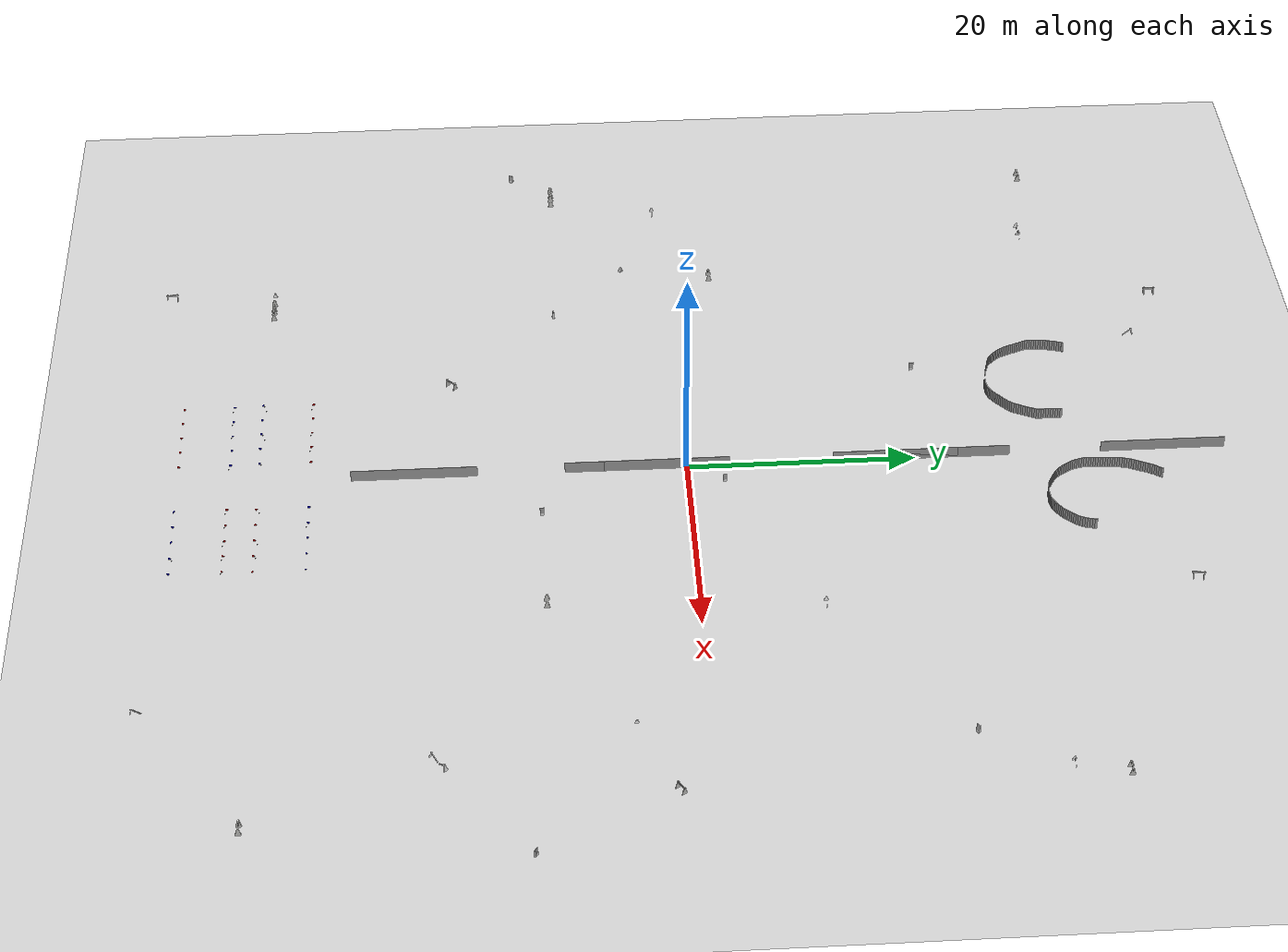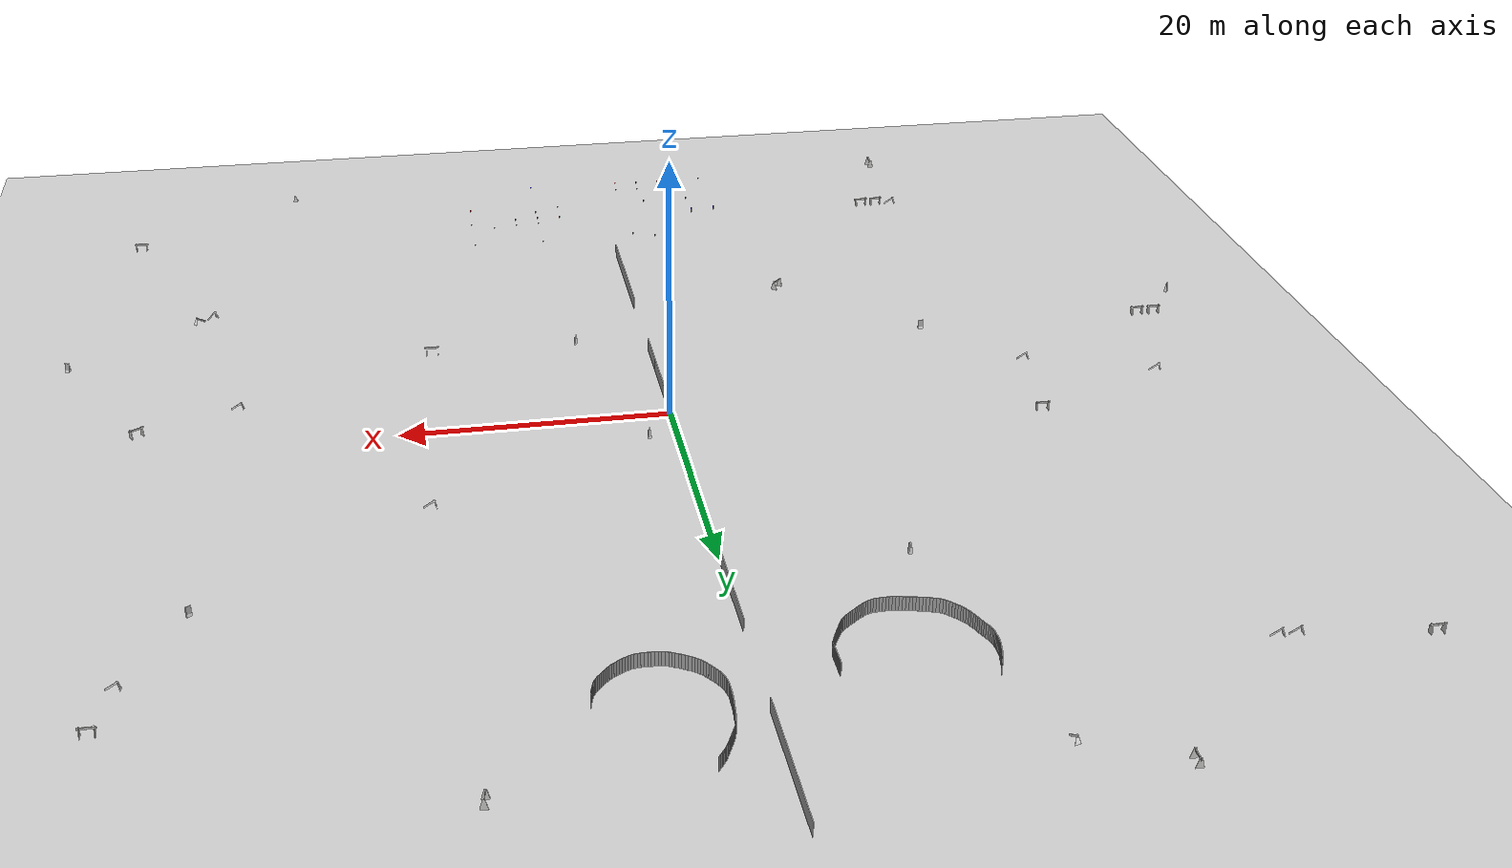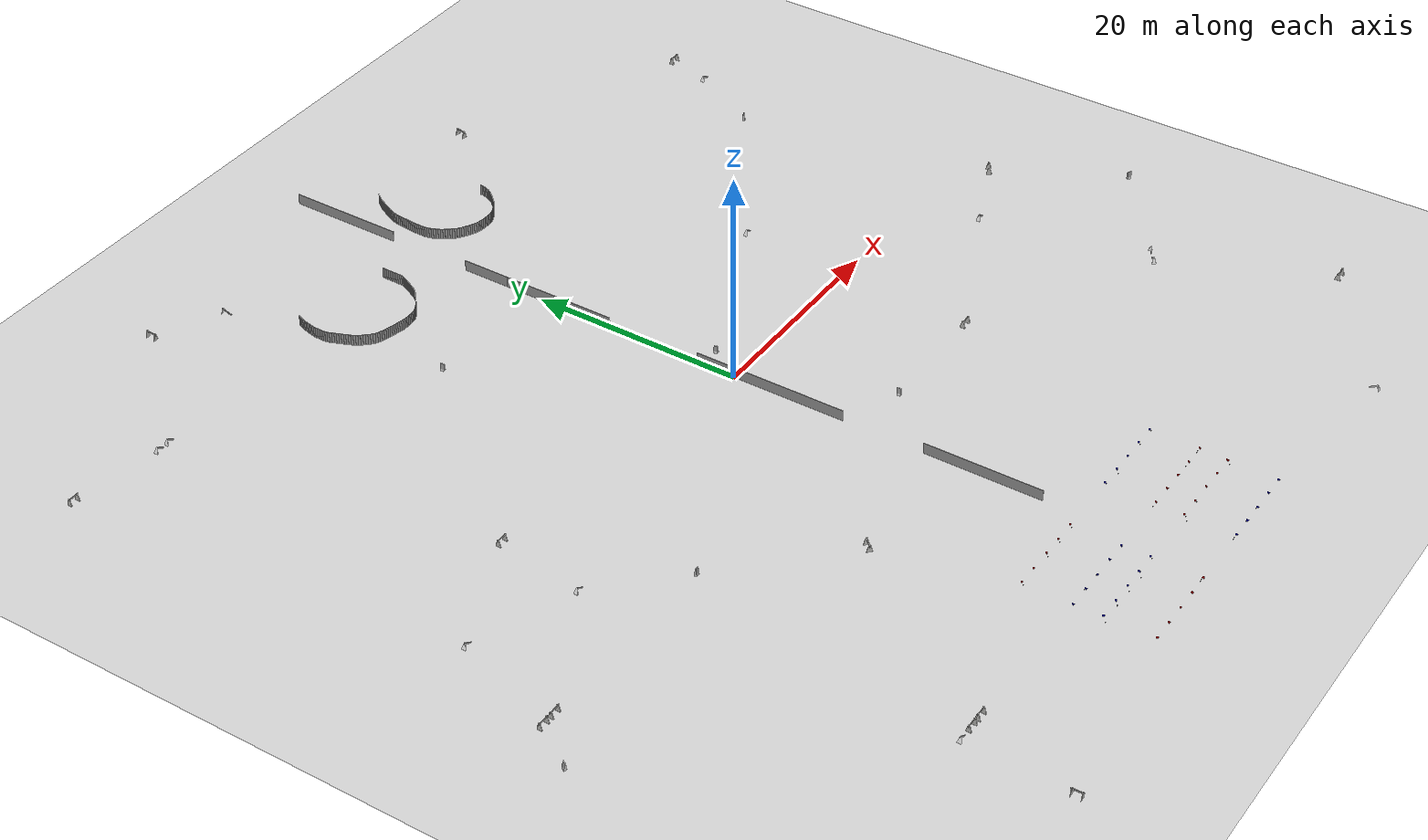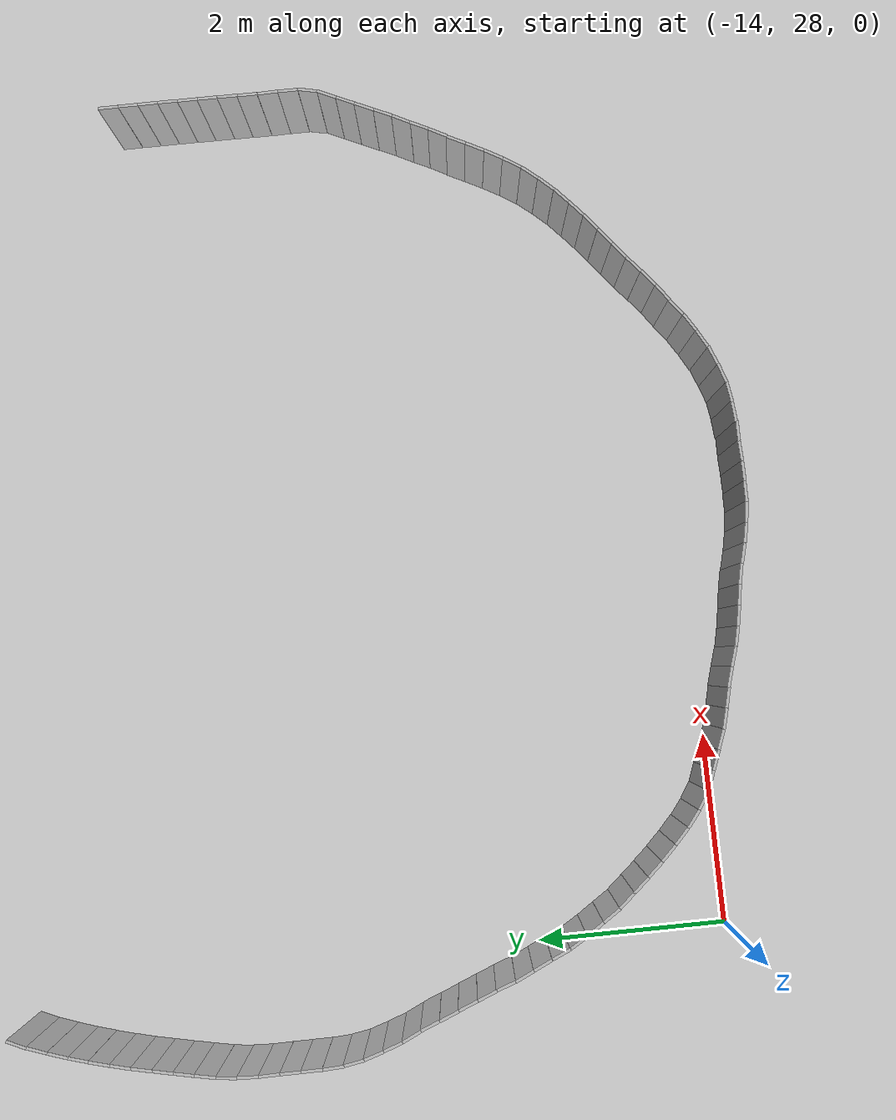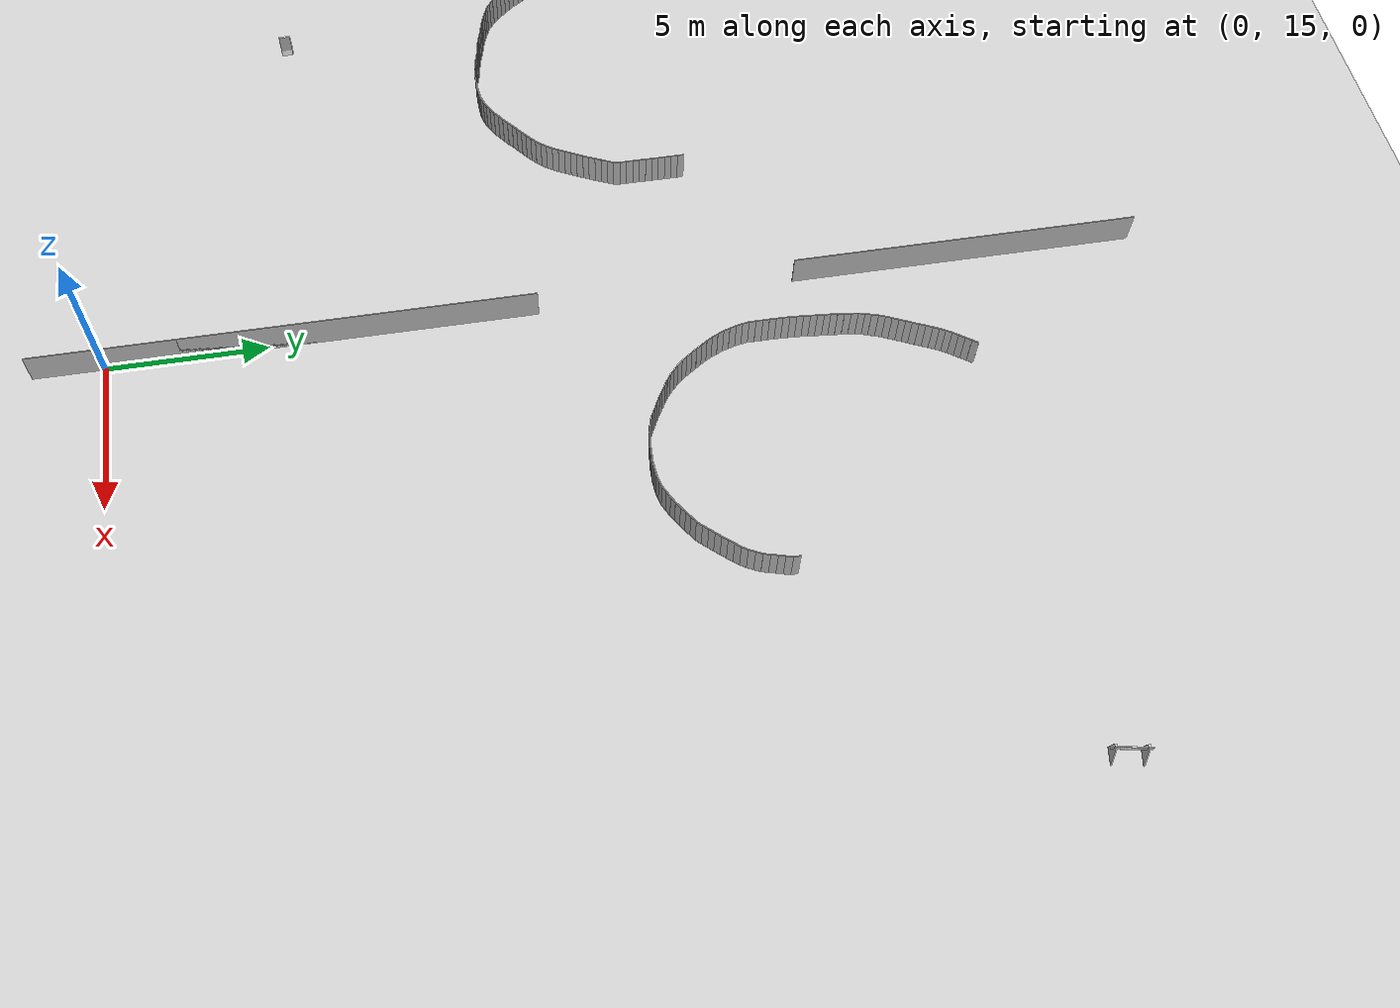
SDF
<sdf version="1.4">
 <world name="default">
  <model name="igvc_advanced_course_plane">
   <static>1</static>
   <link name="link">
    <collision name="collision">
     <geometry><plane><normal>0 0 1</normal><size>100 100</size></plane></geometry>
     <surface><friction><ode><mu>100</mu><mu2>50</mu2></ode></friction></surface>
    </collision>
    <visual name="visual">
     <cast_shadows>0</cast_shadows>
     <geometry><plane><normal>0 0 1</normal><size>100 100</size></plane></geometry>
     <material>
      <script>
       <uri>model://igvc_advanced_course_plane/materials/scripts</uri>
       <uri>model://igvc_advanced_course_plane/materials/textures</uri>
       <name>igvc_advanced_course_plane/Image</name>
      </script>
     </material>
    </visual>
    <velocity_decay><linear>0</linear><angular>0</angular></velocity_decay>
   </link>
  </model>
  <light name="sun" type="directional">
   <pose>0 0 10 0 -0 0</pose>
   <diffuse>0.8 0.8 0.8 1</diffuse>
   <specular>0.2 0.2 0.2 1</specular>
   <attenuation>
    <range>1000</range>
    <constant>0.9</constant>
    <linear>0.01</linear>
    <quadratic>0.001</quadratic>
   </attenuation>
   <direction>-0.5 0.1 -0.9</direction>
  </light>
  <light name="flag_light" type="directional">
   <cast_shadows>0</cast_shadows>
   <pose>-14.5 -39 2 0 -0 0</pose>
   <diffuse>0.5 0.5 0.5 1</diffuse>
   <specular>0.1 0.1 0.1 1</specular>
   <attenuation>
    <range>20</range>
    <constant>0.5</constant>
    <linear>0.01</linear>
    <quadratic>0.001</quadratic>
   </attenuation>
   <direction>0.9 0 0.45</direction>
  </light>
  <physics type="ode">
   <max_step_size>0.001</max_step_size>
   <real_time_factor>1</real_time_factor>
   <real_time_update_rate>1000</real_time_update_rate>
   <gravity>0 0 -9.8</gravity>
  </physics>
  <scene><ambient>0.4 0.4 0.4 1</ambient><background>0.7 0.7 0.7 1</background><shadows>1</shadows></scene>
  <spherical_coordinates>
   <surface_model>EARTH_WGS84</surface_model>
   <latitude_deg>0</latitude_deg>
   <longitude_deg>0</longitude_deg>
   <elevation>0</elevation>
   <heading_deg>0</heading_deg>
  </spherical_coordinates>
  <model name="lattice_245">
   <static>1</static>
   <link name="link">
    <collision name="collision">
     <pose>0.02 0.105 0.525 0 -0 0</pose>
     <geometry><box><size>0.04 0.21 1.05</size></box></geometry>
    </collision>
    <visual name="visual"><geometry><mesh><uri>model://lattice/meshes/lattice.dae</uri></mesh></geometry></visual>
    <velocity_decay><linear>0</linear><angular>0</angular></velocity_decay>
   </link>
   <pose>-14.3852 34.9897 0 0 0 -0.339855</pose>
  </model>
  <model name="lattice_246">
   <static>1</static>
   <link name="link">
    <collision name="collision">
     <pose>0.02 0.105 0.525 0 -0 0</pose>
     <geometry><box><size>0.04 0.21 1.05</size></box></geometry>
    </collision>
    <visual name="visual"><geometry><mesh><uri>model://lattice/meshes/lattice.dae</uri></mesh></geometry></visual>
    <velocity_decay><linear>0</linear><angular>0</angular></velocity_decay>
   </link>
   <pose>-14.3159 35.1904 0 0 0 -0.410077</pose>
  </model>
  <model name="lattice_247">
   <static>1</static>
   <link name="link">
    <collision name="collision">
     <pose>0.02 0.105 0.525 0 -0 0</pose>
     <geometry><box><size>0.04 0.21 1.05</size></box></geometry>
    </collision>
    <visual name="visual"><geometry><mesh><uri>model://lattice/meshes/lattice.dae</uri></mesh></geometry></visual>
    <velocity_decay><linear>0</linear><angular>0</angular></velocity_decay>
   </link>
   <pose>-14.4511 34.7889 0 0 0 -0.313377</pose>
  </model>
  <model name="lattice_248">
   <static>1</static>
   <link name="link">
    <collision name="collision">
     <pose>0.02 0.105 0.525 0 -0 0</pose>
     <geometry><box><size>0.04 0.21 1.05</size></box></geometry>
    </collision>
    <visual name="visual"><geometry><mesh><uri>model://lattice/meshes/lattice.dae</uri></mesh></geometry></visual>
    <velocity_decay><linear>0</linear><angular>0</angular></velocity_decay>
   </link>
   <pose>-14.509 34.5877 0 0 0 -0.277756</pose>
  </model>
  <model name="lattice_249">
   <static>1</static>
   <link name="link">
    <collision name="collision">
     <pose>0.02 0.105 0.525 0 -0 0</pose>
     <geometry><box><size>0.04 0.21 1.05</size></box></geometry>
    </collision>
    <visual name="visual"><geometry><mesh><uri>model://lattice/meshes/lattice.dae</uri></mesh></geometry></visual>
    <velocity_decay><linear>0</linear><angular>0</angular></velocity_decay>
   </link>
   <pose>-14.6157 34.178 0 0 0 -0.246639</pose>
  </model>
  <model name="lattice_250">
   <static>1</static>
   <link name="link">
    <collision name="collision">
     <pose>0.02 0.105 0.525 0 -0 0</pose>
     <geometry><box><size>0.04 0.21 1.05</size></box></geometry>
    </collision>
    <visual name="visual"><geometry><mesh><uri>model://lattice/meshes/lattice.dae</uri></mesh></geometry></visual>
    <velocity_decay><linear>0</linear><angular>0</angular></velocity_decay>
   </link>
   <pose>-14.5651 34.3833 0 0 0 -0.258482</pose>
  </model>
  <model name="lattice_251">
   <static>1</static>
   <link name="link">
    <collision name="collision">
     <pose>0.02 0.105 0.525 0 -0 0</pose>
     <geometry><box><size>0.04 0.21 1.05</size></box></geometry>
    </collision>
    <visual name="visual"><geometry><mesh><uri>model://lattice/meshes/lattice.dae</uri></mesh></geometry></visual>
    <velocity_decay><linear>0</linear><angular>0</angular></velocity_decay>
   </link>
   <pose>-14.6593 33.9689 0 0 0 -0.210782</pose>
  </model>
  <model name="lattice_252">
   <static>1</static>
   <link name="link">
    <collision name="collision">
     <pose>0.02 0.105 0.525 0 -0 0</pose>
     <geometry><box><size>0.04 0.21 1.05</size></box></geometry>
    </collision>
    <visual name="visual"><geometry><mesh><uri>model://lattice/meshes/lattice.dae</uri></mesh></geometry></visual>
    <velocity_decay><linear>0</linear><angular>0</angular></velocity_decay>
   </link>
   <pose>-14.7026 33.7636 0 0 0 -0.2107</pose>
  </model>
  <model name="lattice_253">
   <static>1</static>
   <link name="link">
    <collision name="collision">
     <pose>0.02 0.105 0.525 0 -0 0</pose>
     <geometry><box><size>0.04 0.21 1.05</size></box></geometry>
    </collision>
    <visual name="visual"><geometry><mesh><uri>model://lattice/meshes/lattice.dae</uri></mesh></geometry></visual>
    <velocity_decay><linear>0</linear><angular>0</angular></velocity_decay>
   </link>
   <pose>-14.7437 33.5598 0 0 0 -0.203867</pose>
  </model>
  <model name="lattice_254">
   <static>1</static>
   <link name="link">
    <collision name="collision">
     <pose>0.02 0.105 0.525 0 -0 0</pose>
     <geometry><box><size>0.04 0.21 1.05</size></box></geometry>
    </collision>
    <visual name="visual"><geometry><mesh><uri>model://lattice/meshes/lattice.dae</uri></mesh></geometry></visual>
    <velocity_decay><linear>0</linear><angular>0</angular></velocity_decay>
   </link>
   <pose>-14.8122 32.2959 0 0 -0 0</pose>
  </model>
  <model name="lattice_255">
   <static>1</static>
   <link name="link">
    <collision name="collision">
     <pose>0.02 0.105 0.525 0 -0 0</pose>
     <geometry><box><size>0.04 0.21 1.05</size></box></geometry>
    </collision>
    <visual name="visual"><geometry><mesh><uri>model://lattice/meshes/lattice.dae</uri></mesh></geometry></visual>
    <velocity_decay><linear>0</linear><angular>0</angular></velocity_decay>
   </link>
   <pose>-14.8016 32.0816 0 0 -0 0.05528</pose>
  </model>
  <model name="lattice_256">
   <static>1</static>
   <link name="link">
    <collision name="collision">
     <pose>0.02 0.105 0.525 0 -0 0</pose>
     <geometry><box><size>0.04 0.21 1.05</size></box></geometry>
    </collision>
    <visual name="visual"><geometry><mesh><uri>model://lattice/meshes/lattice.dae</uri></mesh></geometry></visual>
    <velocity_decay><linear>0</linear><angular>0</angular></velocity_decay>
   </link>
   <pose>-14.7838 33.3525 0 0 0 -0.194191</pose>
  </model>
  <model name="lattice_257">
   <static>1</static>
   <link name="link">
    <collision name="collision">
     <pose>0.02 0.105 0.525 0 -0 0</pose>
     <geometry><box><size>0.04 0.21 1.05</size></box></geometry>
    </collision>
    <visual name="visual"><geometry><mesh><uri>model://lattice/meshes/lattice.dae</uri></mesh></geometry></visual>
    <velocity_decay><linear>0</linear><angular>0</angular></velocity_decay>
   </link>
   <pose>-14.8085 33.1399 0 0 0 -0.109519</pose>
  </model>
  <model name="lattice_258">
   <static>1</static>
   <link name="link">
    <collision name="collision">
     <pose>0.02 0.105 0.525 0 -0 0</pose>
     <geometry><box><size>0.04 0.21 1.05</size></box></geometry>
    </collision>
    <visual name="visual"><geometry><mesh><uri>model://lattice/meshes/lattice.dae</uri></mesh></geometry></visual>
    <velocity_decay><linear>0</linear><angular>0</angular></velocity_decay>
   </link>
   <pose>-14.813 32.7171 0 0 -0 0.01741</pose>
  </model>
  <model name="lattice_259">
   <static>1</static>
   <link name="link">
    <collision name="collision">
     <pose>0.02 0.105 0.525 0 -0 0</pose>
     <geometry><box><size>0.04 0.21 1.05</size></box></geometry>
    </collision>
    <visual name="visual"><geometry><mesh><uri>model://lattice/meshes/lattice.dae</uri></mesh></geometry></visual>
    <velocity_decay><linear>0</linear><angular>0</angular></velocity_decay>
   </link>
   <pose>-14.8173 32.9285 0 0 0 -0.053532</pose>
  </model>
  <model name="lattice_260">
   <static>1</static>
   <link name="link">
    <collision name="collision">
     <pose>0.02 0.105 0.525 0 -0 0</pose>
     <geometry><box><size>0.04 0.21 1.05</size></box></geometry>
    </collision>
    <visual name="visual"><geometry><mesh><uri>model://lattice/meshes/lattice.dae</uri></mesh></geometry></visual>
    <velocity_decay><linear>0</linear><angular>0</angular></velocity_decay>
   </link>
   <pose>-14.8134 32.5066 0 0 -0 0</pose>
  </model>
  <model name="lattice_261">
   <static>1</static>
   <link name="link">
    <collision name="collision">
     <pose>0.02 0.105 0.525 0 -0 0</pose>
     <geometry><box><size>0.04 0.21 1.05</size></box></geometry>
    </collision>
    <visual name="visual"><geometry><mesh><uri>model://lattice/meshes/lattice.dae</uri></mesh></geometry></visual>
    <velocity_decay><linear>0</linear><angular>0</angular></velocity_decay>
   </link>
   <pose>-14.7645 31.8748 0 0 -0 0.166525</pose>
  </model>
  <model name="lattice_262">
   <static>1</static>
   <link name="link">
    <collision name="collision">
     <pose>0.02 0.105 0.525 0 -0 0</pose>
     <geometry><box><size>0.04 0.21 1.05</size></box></geometry>
    </collision>
    <visual name="visual"><geometry><mesh><uri>model://lattice/meshes/lattice.dae</uri></mesh></geometry></visual>
    <velocity_decay><linear>0</linear><angular>0</angular></velocity_decay>
   </link>
   <pose>-14.6332 31.48 0 0 -0 0.323678</pose>
  </model>
  <model name="lattice_263">
   <static>1</static>
   <link name="link">
    <collision name="collision">
     <pose>0.02 0.105 0.525 0 -0 0</pose>
     <geometry><box><size>0.04 0.21 1.05</size></box></geometry>
    </collision>
    <visual name="visual"><geometry><mesh><uri>model://lattice/meshes/lattice.dae</uri></mesh></geometry></visual>
    <velocity_decay><linear>0</linear><angular>0</angular></velocity_decay>
   </link>
   <pose>-14.5429 31.2881 0 0 -0 0.437579</pose>
  </model>
  <model name="lattice_264">
   <static>1</static>
   <link name="link">
    <collision name="collision">
     <pose>0.02 0.105 0.525 0 -0 0</pose>
     <geometry><box><size>0.04 0.21 1.05</size></box></geometry>
    </collision>
    <visual name="visual"><geometry><mesh><uri>model://lattice/meshes/lattice.dae</uri></mesh></geometry></visual>
    <velocity_decay><linear>0</linear><angular>0</angular></velocity_decay>
   </link>
   <pose>-14.16 30.3075 0 0 -0 0.335858</pose>
  </model>
  <model name="lattice_265">
   <static>1</static>
   <link name="link">
    <collision name="collision">
     <pose>0.02 0.105 0.525 0 -0 0</pose>
     <geometry><box><size>0.04 0.21 1.05</size></box></geometry>
    </collision>
    <visual name="visual"><geometry><mesh><uri>model://lattice/meshes/lattice.dae</uri></mesh></geometry></visual>
    <velocity_decay><linear>0</linear><angular>0</angular></velocity_decay>
   </link>
   <pose>-14.3877 30.8988 0 0 -0 0.383417</pose>
  </model>
  <model name="lattice_266">
   <static>1</static>
   <link name="link">
    <collision name="collision">
     <pose>0.02 0.105 0.525 0 -0 0</pose>
     <geometry><box><size>0.04 0.21 1.05</size></box></geometry>
    </collision>
    <visual name="visual"><geometry><mesh><uri>model://lattice/meshes/lattice.dae</uri></mesh></geometry></visual>
    <velocity_decay><linear>0</linear><angular>0</angular></velocity_decay>
   </link>
   <pose>-14.4626 31.0923 0 0 -0 0.377834</pose>
  </model>
  <model name="lattice_267">
   <static>1</static>
   <link name="link">
    <collision name="collision">
     <pose>0.02 0.105 0.525 0 -0 0</pose>
     <geometry><box><size>0.04 0.21 1.05</size></box></geometry>
    </collision>
    <visual name="visual"><geometry><mesh><uri>model://lattice/meshes/lattice.dae</uri></mesh></geometry></visual>
    <velocity_decay><linear>0</linear><angular>0</angular></velocity_decay>
   </link>
   <pose>-14.2291 30.5009 0 0 -0 0.378967</pose>
  </model>
  <model name="lattice_268">
   <static>1</static>
   <link name="link">
    <collision name="collision">
     <pose>0.02 0.105 0.525 0 -0 0</pose>
     <geometry><box><size>0.04 0.21 1.05</size></box></geometry>
    </collision>
    <visual name="visual"><geometry><mesh><uri>model://lattice/meshes/lattice.dae</uri></mesh></geometry></visual>
    <velocity_decay><linear>0</linear><angular>0</angular></velocity_decay>
   </link>
   <pose>-14.3067 30.7001 0 0 -0 0.378915</pose>
  </model>
  <model name="lattice_269">
   <static>1</static>
   <link name="link">
    <collision name="collision">
     <pose>0.02 0.105 0.525 0 -0 0</pose>
     <geometry><box><size>0.04 0.21 1.05</size></box></geometry>
    </collision>
    <visual name="visual"><geometry><mesh><uri>model://lattice/meshes/lattice.dae</uri></mesh></geometry></visual>
    <velocity_decay><linear>0</linear><angular>0</angular></velocity_decay>
   </link>
   <pose>-14.7023 31.6766 0 0 -0 0.298199</pose>
  </model>
  <model name="lattice_270">
   <static>1</static>
   <link name="link">
    <collision name="collision">
     <pose>0.02 0.105 0.525 0 -0 0</pose>
     <geometry><box><size>0.04 0.21 1.05</size></box></geometry>
    </collision>
    <visual name="visual"><geometry><mesh><uri>model://lattice/meshes/lattice.dae</uri></mesh></geometry></visual>
    <velocity_decay><linear>0</linear><angular>0</angular></velocity_decay>
   </link>
   <pose>-14.076 30.1159 0 0 -0 0.424812</pose>
  </model>
  <model name="lattice_271">
   <static>1</static>
   <link name="link">
    <collision name="collision">
     <pose>0.02 0.105 0.525 0 -0 0</pose>
     <geometry><box><size>0.04 0.21 1.05</size></box></geometry>
    </collision>
    <visual name="visual"><geometry><mesh><uri>model://lattice/meshes/lattice.dae</uri></mesh></geometry></visual>
    <velocity_decay><linear>0</linear><angular>0</angular></velocity_decay>
   </link>
   <pose>-13.9011 29.7295 0 0 -0 0.408534</pose>
  </model>
  <model name="lattice_272">
   <static>1</static>
   <link name="link">
    <collision name="collision">
     <pose>0.02 0.105 0.525 0 -0 0</pose>
     <geometry><box><size>0.04 0.21 1.05</size></box></geometry>
    </collision>
    <visual name="visual"><geometry><mesh><uri>model://lattice/meshes/lattice.dae</uri></mesh></geometry></visual>
    <velocity_decay><linear>0</linear><angular>0</angular></velocity_decay>
   </link>
   <pose>-13.9865 29.9248 0 0 -0 0.429621</pose>
  </model>
  <model name="lattice_273">
   <static>1</static>
   <link name="link">
    <collision name="collision">
     <pose>0.02 0.105 0.525 0 -0 0</pose>
     <geometry><box><size>0.04 0.21 1.05</size></box></geometry>
    </collision>
    <visual name="visual"><geometry><mesh><uri>model://lattice/meshes/lattice.dae</uri></mesh></geometry></visual>
    <velocity_decay><linear>0</linear><angular>0</angular></velocity_decay>
   </link>
   <pose>-13.7941 29.552 0 0 -0 0.540804</pose>
  </model>
  <model name="lattice_274">
   <static>1</static>
   <link name="link">
    <collision name="collision">
     <pose>0.02 0.105 0.525 0 -0 0</pose>
     <geometry><box><size>0.04 0.21 1.05</size></box></geometry>
    </collision>
    <visual name="visual"><geometry><mesh><uri>model://lattice/meshes/lattice.dae</uri></mesh></geometry></visual>
    <velocity_decay><linear>0</linear><angular>0</angular></velocity_decay>
   </link>
   <pose>-13.6753 29.3738 0 0 -0 0.592553</pose>
  </model>
  <model name="lattice_275">
   <static>1</static>
   <link name="link">
    <collision name="collision">
     <pose>0.02 0.105 0.525 0 -0 0</pose>
     <geometry><box><size>0.04 0.21 1.05</size></box></geometry>
    </collision>
    <visual name="visual"><geometry><mesh><uri>model://lattice/meshes/lattice.dae</uri></mesh></geometry></visual>
    <velocity_decay><linear>0</linear><angular>0</angular></velocity_decay>
   </link>
   <pose>-13.2845 28.8792 0 0 -0 0.713262</pose>
  </model>
  <model name="lattice_276">
   <static>1</static>
   <link name="link">
    <collision name="collision">
     <pose>0.02 0.105 0.525 0 -0 0</pose>
     <geometry><box><size>0.04 0.21 1.05</size></box></geometry>
    </collision>
    <visual name="visual"><geometry><mesh><uri>model://lattice/meshes/lattice.dae</uri></mesh></geometry></visual>
    <velocity_decay><linear>0</linear><angular>0</angular></velocity_decay>
   </link>
   <pose>-13.1398 28.7208 0 0 -0 0.725736</pose>
  </model>
  <model name="lattice_277">
   <static>1</static>
   <link name="link">
    <collision name="collision">
     <pose>0.02 0.105 0.525 0 -0 0</pose>
     <geometry><box><size>0.04 0.21 1.05</size></box></geometry>
    </collision>
    <visual name="visual"><geometry><mesh><uri>model://lattice/meshes/lattice.dae</uri></mesh></geometry></visual>
    <velocity_decay><linear>0</linear><angular>0</angular></velocity_decay>
   </link>
   <pose>-12.9911 28.5724 0 0 -0 0.773233</pose>
  </model>
  <model name="lattice_278">
   <static>1</static>
   <link name="link">
    <collision name="collision">
     <pose>0.02 0.105 0.525 0 -0 0</pose>
     <geometry><box><size>0.04 0.21 1.05</size></box></geometry>
    </collision>
    <visual name="visual"><geometry><mesh><uri>model://lattice/meshes/lattice.dae</uri></mesh></geometry></visual>
    <velocity_decay><linear>0</linear><angular>0</angular></velocity_decay>
   </link>
   <pose>-13.4173 29.0337 0 0 -0 0.708285</pose>
  </model>
  <model name="lattice_279">
   <static>1</static>
   <link name="link">
    <collision name="collision">
     <pose>0.02 0.105 0.525 0 -0 0</pose>
     <geometry><box><size>0.04 0.21 1.05</size></box></geometry>
    </collision>
    <visual name="visual"><geometry><mesh><uri>model://lattice/meshes/lattice.dae</uri></mesh></geometry></visual>
    <velocity_decay><linear>0</linear><angular>0</angular></velocity_decay>
   </link>
   <pose>-13.5594 29.1965 0 0 -0 0.579834</pose>
  </model>
  <model name="lattice_280">
   <static>1</static>
   <link name="link">
    <collision name="collision">
     <pose>0.02 0.105 0.525 0 -0 0</pose>
     <geometry><box><size>0.04 0.21 1.05</size></box></geometry>
    </collision>
    <visual name="visual"><geometry><mesh><uri>model://lattice/meshes/lattice.dae</uri></mesh></geometry></visual>
    <velocity_decay><linear>0</linear><angular>0</angular></velocity_decay>
   </link>
   <pose>-12.8342 28.4268 0 0 -0 0.817831</pose>
  </model>
  <model name="lattice_281">
   <static>1</static>
   <link name="link">
    <collision name="collision">
     <pose>0.02 0.105 0.525 0 -0 0</pose>
     <geometry><box><size>0.04 0.21 1.05</size></box></geometry>
    </collision>
    <visual name="visual"><geometry><mesh><uri>model://lattice/meshes/lattice.dae</uri></mesh></geometry></visual>
    <velocity_decay><linear>0</linear><angular>0</angular></velocity_decay>
   </link>
   <pose>-12.67 28.2961 0 0 -0 0.909354</pose>
  </model>
  <model name="lattice_282">
   <static>1</static>
   <link name="link">
    <collision name="collision">
     <pose>0.02 0.105 0.525 0 -0 0</pose>
     <geometry><box><size>0.04 0.21 1.05</size></box></geometry>
    </collision>
    <visual name="visual"><geometry><mesh><uri>model://lattice/meshes/lattice.dae</uri></mesh></geometry></visual>
    <velocity_decay><linear>0</linear><angular>0</angular></velocity_decay>
   </link>
   <pose>-12.2892 28.1071 0 0 -0 1.21471</pose>
  </model>
  <model name="lattice_284">
   <static>1</static>
   <link name="link">
    <collision name="collision">
     <pose>0.02 0.105 0.525 0 -0 0</pose>
     <geometry><box><size>0.04 0.21 1.05</size></box></geometry>
    </collision>
    <visual name="visual"><geometry><mesh><uri>model://lattice/meshes/lattice.dae</uri></mesh></geometry></visual>
    <velocity_decay><linear>0</linear><angular>0</angular></velocity_decay>
   </link>
   <pose>-12.0926 28.03 0 0 -0 1.19906</pose>
  </model>
  <model name="lattice_285">
   <static>1</static>
   <link name="link">
    <collision name="collision">
     <pose>0.02 0.105 0.525 0 -0 0</pose>
     <geometry><box><size>0.04 0.21 1.05</size></box></geometry>
    </collision>
    <visual name="visual"><geometry><mesh><uri>model://lattice/meshes/lattice.dae</uri></mesh></geometry></visual>
    <velocity_decay><linear>0</linear><angular>0</angular></velocity_decay>
   </link>
   <pose>-12.4913 28.1819 0 0 -0 0.996988</pose>
  </model>
  <model name="lattice_286">
   <static>1</static>
   <link name="link">
    <collision name="collision">
     <pose>0.02 0.105 0.525 0 -0 0</pose>
     <geometry><box><size>0.04 0.21 1.05</size></box></geometry>
    </collision>
    <visual name="visual"><geometry><mesh><uri>model://lattice/meshes/lattice.dae</uri></mesh></geometry></visual>
    <velocity_decay><linear>0</linear><angular>0</angular></velocity_decay>
   </link>
   <pose>-11.8907 27.9574 0 0 -0 1.21367</pose>
  </model>
  <model name="lattice_287">
   <static>1</static>
   <link name="link">
    <collision name="collision">
     <pose>0.02 0.105 0.525 0 -0 0</pose>
     <geometry><box><size>0.04 0.21 1.05</size></box></geometry>
    </collision>
    <visual name="visual"><geometry><mesh><uri>model://lattice/meshes/lattice.dae</uri></mesh></geometry></visual>
    <velocity_decay><linear>0</linear><angular>0</angular></velocity_decay>
   </link>
   <pose>-11.6854 27.9033 0 0 -0 1.32053</pose>
  </model>
  <model name="lattice_288">
   <static>1</static>
   <link name="link">
    <collision name="collision">
     <pose>0.02 0.105 0.525 0 -0 0</pose>
     <geometry><box><size>0.04 0.21 1.05</size></box></geometry>
    </collision>
    <visual name="visual"><geometry><mesh><uri>model://lattice/meshes/lattice.dae</uri></mesh></geometry></visual>
    <velocity_decay><linear>0</linear><angular>0</angular></velocity_decay>
   </link>
   <pose>-11.478 27.8548 0 0 -0 1.33418</pose>
  </model>
  <model name="lattice_289">
   <static>1</static>
   <link name="link">
    <collision name="collision">
     <pose>0.02 0.105 0.525 0 -0 0</pose>
     <geometry><box><size>0.04 0.21 1.05</size></box></geometry>
    </collision>
    <visual name="visual"><geometry><mesh><uri>model://lattice/meshes/lattice.dae</uri></mesh></geometry></visual>
    <velocity_decay><linear>0</linear><angular>0</angular></velocity_decay>
   </link>
   <pose>-11.277 27.8021 0 0 -0 1.29458</pose>
  </model>
  <model name="lattice_290">
   <static>1</static>
   <link name="link">
    <collision name="collision">
     <pose>0.02 0.105 0.525 0 -0 0</pose>
     <geometry><box><size>0.04 0.21 1.05</size></box></geometry>
    </collision>
    <visual name="visual"><geometry><mesh><uri>model://lattice/meshes/lattice.dae</uri></mesh></geometry></visual>
    <velocity_decay><linear>0</linear><angular>0</angular></velocity_decay>
   </link>
   <pose>-11.0762 27.7398 0 0 -0 1.27098</pose>
  </model>
  <model name="lattice_291">
   <static>1</static>
   <link name="link">
    <collision name="collision">
     <pose>0.02 0.105 0.525 0 -0 0</pose>
     <geometry><box><size>0.04 0.21 1.05</size></box></geometry>
    </collision>
    <visual name="visual"><geometry><mesh><uri>model://lattice/meshes/lattice.dae</uri></mesh></geometry></visual>
    <velocity_decay><linear>0</linear><angular>0</angular></velocity_decay>
   </link>
   <pose>-10.8722 27.6923 0 0 -0 1.35266</pose>
  </model>
  <model name="lattice_292">
   <static>1</static>
   <link name="link">
    <collision name="collision">
     <pose>0.02 0.105 0.525 0 -0 0</pose>
     <geometry><box><size>0.04 0.21 1.05</size></box></geometry>
    </collision>
    <visual name="visual"><geometry><mesh><uri>model://lattice/meshes/lattice.dae</uri></mesh></geometry></visual>
    <velocity_decay><linear>0</linear><angular>0</angular></velocity_decay>
   </link>
   <pose>-10.4522 27.623 0 0 -0 1.41487</pose>
  </model>
  <model name="lattice_293">
   <static>1</static>
   <link name="link">
    <collision name="collision">
     <pose>0.02 0.105 0.525 0 -0 0</pose>
     <geometry><box><size>0.04 0.21 1.05</size></box></geometry>
    </collision>
    <visual name="visual"><geometry><mesh><uri>model://lattice/meshes/lattice.dae</uri></mesh></geometry></visual>
    <velocity_decay><linear>0</linear><angular>0</angular></velocity_decay>
   </link>
   <pose>-10.6625 27.6556 0 0 -0 1.3969</pose>
  </model>
  <model name="lattice_294">
   <static>1</static>
   <link name="link">
    <collision name="collision">
     <pose>0.02 0.105 0.525 0 -0 0</pose>
     <geometry><box><size>0.04 0.21 1.05</size></box></geometry>
    </collision>
    <visual name="visual"><geometry><mesh><uri>model://lattice/meshes/lattice.dae</uri></mesh></geometry></visual>
    <velocity_decay><linear>0</linear><angular>0</angular></velocity_decay>
   </link>
   <pose>-10.041 27.5252 0 0 -0 1.31818</pose>
  </model>
  <model name="lattice_295">
   <static>1</static>
   <link name="link">
    <collision name="collision">
     <pose>0.02 0.105 0.525 0 -0 0</pose>
     <geometry><box><size>0.04 0.21 1.05</size></box></geometry>
    </collision>
    <visual name="visual"><geometry><mesh><uri>model://lattice/meshes/lattice.dae</uri></mesh></geometry></visual>
    <velocity_decay><linear>0</linear><angular>0</angular></velocity_decay>
   </link>
   <pose>-10.2432 27.5811 0 0 -0 1.36789</pose>
  </model>
  <model name="lattice_296">
   <static>1</static>
   <link name="link">
    <collision name="collision">
     <pose>0.02 0.105 0.525 0 -0 0</pose>
     <geometry><box><size>0.04 0.21 1.05</size></box></geometry>
    </collision>
    <visual name="visual"><geometry><mesh><uri>model://lattice/meshes/lattice.dae</uri></mesh></geometry></visual>
    <velocity_decay><linear>0</linear><angular>0</angular></velocity_decay>
   </link>
   <pose>-9.83035 27.4835 0 0 -0 1.38099</pose>
  </model>
  <model name="lattice_298">
   <static>1</static>
   <link name="link">
    <collision name="collision">
     <pose>0.02 0.105 0.525 0 -0 0</pose>
     <geometry><box><size>0.04 0.21 1.05</size></box></geometry>
    </collision>
    <visual name="visual"><geometry><mesh><uri>model://lattice/meshes/lattice.dae</uri></mesh></geometry></visual>
    <velocity_decay><linear>0</linear><angular>0</angular></velocity_decay>
   </link>
   <pose>-9.61835 27.4553 0 0 -0 1.43847</pose>
  </model>
  <model name="lattice_299">
   <static>1</static>
   <link name="link">
    <collision name="collision">
     <pose>0.02 0.105 0.525 0 -0 0</pose>
     <geometry><box><size>0.04 0.21 1.05</size></box></geometry>
    </collision>
    <visual name="visual"><geometry><mesh><uri>model://lattice/meshes/lattice.dae</uri></mesh></geometry></visual>
    <velocity_decay><linear>0</linear><angular>0</angular></velocity_decay>
   </link>
   <pose>-9.61185 27.484 0 0 0 -1.57376</pose>
  </model>
  <model name="lattice_300">
   <static>1</static>
   <link name="link">
    <collision name="collision">
     <pose>0.02 0.105 0.525 0 -0 0</pose>
     <geometry><box><size>0.04 0.21 1.05</size></box></geometry>
    </collision>
    <visual name="visual"><geometry><mesh><uri>model://lattice/meshes/lattice.dae</uri></mesh></geometry></visual>
    <velocity_decay><linear>0</linear><angular>0</angular></velocity_decay>
   </link>
   <pose>-9.19842 27.4518 0 0 -0 1.58113</pose>
  </model>
  <model name="lattice_301">
   <static>1</static>
   <link name="link">
    <collision name="collision">
     <pose>0.02 0.105 0.525 0 -0 0</pose>
     <geometry><box><size>0.04 0.21 1.05</size></box></geometry>
    </collision>
    <visual name="visual"><geometry><mesh><uri>model://lattice/meshes/lattice.dae</uri></mesh></geometry></visual>
    <velocity_decay><linear>0</linear><angular>0</angular></velocity_decay>
   </link>
   <pose>-8.98328 27.4612 0 0 -0 1.61743</pose>
  </model>
  <model name="lattice_302">
   <static>1</static>
   <link name="link">
    <collision name="collision">
     <pose>0.02 0.105 0.525 0 -0 0</pose>
     <geometry><box><size>0.04 0.21 1.05</size></box></geometry>
    </collision>
    <visual name="visual"><geometry><mesh><uri>model://lattice/meshes/lattice.dae</uri></mesh></geometry></visual>
    <velocity_decay><linear>0</linear><angular>0</angular></velocity_decay>
   </link>
   <pose>-8.77565 27.4585 0 0 -0 1.56845</pose>
  </model>
  <model name="lattice_303">
   <static>1</static>
   <link name="link">
    <collision name="collision">
     <pose>0.02 0.105 0.525 0 -0 0</pose>
     <geometry><box><size>0.04 0.21 1.05</size></box></geometry>
    </collision>
    <visual name="visual"><geometry><mesh><uri>model://lattice/meshes/lattice.dae</uri></mesh></geometry></visual>
    <velocity_decay><linear>0</linear><angular>0</angular></velocity_decay>
   </link>
   <pose>-8.5677 27.4842 0 0 -0 1.66164</pose>
  </model>
  <model name="lattice_304">
   <static>1</static>
   <link name="link">
    <collision name="collision">
     <pose>0.02 0.105 0.525 0 -0 0</pose>
     <geometry><box><size>0.04 0.21 1.05</size></box></geometry>
    </collision>
    <visual name="visual"><geometry><mesh><uri>model://lattice/meshes/lattice.dae</uri></mesh></geometry></visual>
    <velocity_decay><linear>0</linear><angular>0</angular></velocity_decay>
   </link>
   <pose>-8.3636 27.5149 0 0 -0 1.72796</pose>
  </model>
  <model name="lattice_305">
   <static>1</static>
   <link name="link">
    <collision name="collision">
     <pose>0.02 0.105 0.525 0 -0 0</pose>
     <geometry><box><size>0.04 0.21 1.05</size></box></geometry>
    </collision>
    <visual name="visual"><geometry><mesh><uri>model://lattice/meshes/lattice.dae</uri></mesh></geometry></visual>
    <velocity_decay><linear>0</linear><angular>0</angular></velocity_decay>
   </link>
   <pose>-8.1592 27.5829 0 0 -0 1.89307</pose>
  </model>
  <model name="lattice_306">
   <static>1</static>
   <link name="link">
    <collision name="collision">
     <pose>0.02 0.105 0.525 0 -0 0</pose>
     <geometry><box><size>0.04 0.21 1.05</size></box></geometry>
    </collision>
    <visual name="visual"><geometry><mesh><uri>model://lattice/meshes/lattice.dae</uri></mesh></geometry></visual>
    <velocity_decay><linear>0</linear><angular>0</angular></velocity_decay>
   </link>
   <pose>-7.60734 27.8774 0 0 -0 2.13225</pose>
  </model>
  <model name="lattice_307">
   <static>1</static>
   <link name="link">
    <collision name="collision">
     <pose>0.02 0.105 0.525 0 -0 0</pose>
     <geometry><box><size>0.04 0.21 1.05</size></box></geometry>
    </collision>
    <visual name="visual"><geometry><mesh><uri>model://lattice/meshes/lattice.dae</uri></mesh></geometry></visual>
    <velocity_decay><linear>0</linear><angular>0</angular></velocity_decay>
   </link>
   <pose>-7.96972 27.6591 0 0 -0 1.93855</pose>
  </model>
  <model name="lattice_308">
   <static>1</static>
   <link name="link">
    <collision name="collision">
     <pose>0.02 0.105 0.525 0 -0 0</pose>
     <geometry><box><size>0.04 0.21 1.05</size></box></geometry>
    </collision>
    <visual name="visual"><geometry><mesh><uri>model://lattice/meshes/lattice.dae</uri></mesh></geometry></visual>
    <velocity_decay><linear>0</linear><angular>0</angular></velocity_decay>
   </link>
   <pose>-7.78782 27.7645 0 0 -0 2.07382</pose>
  </model>
  <model name="lattice_309">
   <static>1</static>
   <link name="link">
    <collision name="collision">
     <pose>0.02 0.105 0.525 0 -0 0</pose>
     <geometry><box><size>0.04 0.21 1.05</size></box></geometry>
    </collision>
    <visual name="visual"><geometry><mesh><uri>model://lattice/meshes/lattice.dae</uri></mesh></geometry></visual>
    <velocity_decay><linear>0</linear><angular>0</angular></velocity_decay>
   </link>
   <pose>-6.45201 28.7935 0 0 -0 2.23524</pose>
  </model>
  <model name="lattice_310">
   <static>1</static>
   <link name="link">
    <collision name="collision">
     <pose>0.02 0.105 0.525 0 -0 0</pose>
     <geometry><box><size>0.04 0.21 1.05</size></box></geometry>
    </collision>
    <visual name="visual"><geometry><mesh><uri>model://lattice/meshes/lattice.dae</uri></mesh></geometry></visual>
    <velocity_decay><linear>0</linear><angular>0</angular></velocity_decay>
   </link>
   <pose>-6.94274 28.4025 0 0 -0 2.27051</pose>
  </model>
  <model name="lattice_311">
   <static>1</static>
   <link name="link">
    <collision name="collision">
     <pose>0.02 0.105 0.525 0 -0 0</pose>
     <geometry><box><size>0.04 0.21 1.05</size></box></geometry>
    </collision>
    <visual name="visual"><geometry><mesh><uri>model://lattice/meshes/lattice.dae</uri></mesh></geometry></visual>
    <velocity_decay><linear>0</linear><angular>0</angular></velocity_decay>
   </link>
   <pose>-7.45187 28.0336 0 0 0 -0.953021</pose>
  </model>
  <model name="lattice_312">
   <static>1</static>
   <link name="link">
    <collision name="collision">
     <pose>0.02 0.105 0.525 0 -0 0</pose>
     <geometry><box><size>0.04 0.21 1.05</size></box></geometry>
    </collision>
    <visual name="visual"><geometry><mesh><uri>model://lattice/meshes/lattice.dae</uri></mesh></geometry></visual>
    <velocity_decay><linear>0</linear><angular>0</angular></velocity_decay>
   </link>
   <pose>-7.61783 27.9063 0 0 0 -0.899923</pose>
  </model>
  <model name="lattice_313">
   <static>1</static>
   <link name="link">
    <collision name="collision">
     <pose>0.02 0.105 0.525 0 -0 0</pose>
     <geometry><box><size>0.04 0.21 1.05</size></box></geometry>
    </collision>
    <visual name="visual"><geometry><mesh><uri>model://lattice/meshes/lattice.dae</uri></mesh></geometry></visual>
    <velocity_decay><linear>0</linear><angular>0</angular></velocity_decay>
   </link>
   <pose>-6.61446 28.6625 0 0 -0 2.24333</pose>
  </model>
  <model name="lattice_314">
   <static>1</static>
   <link name="link">
    <collision name="collision">
     <pose>0.02 0.105 0.525 0 -0 0</pose>
     <geometry><box><size>0.04 0.21 1.05</size></box></geometry>
    </collision>
    <visual name="visual"><geometry><mesh><uri>model://lattice/meshes/lattice.dae</uri></mesh></geometry></visual>
    <velocity_decay><linear>0</linear><angular>0</angular></velocity_decay>
   </link>
   <pose>-6.29471 28.9329 0 0 -0 2.29245</pose>
  </model>
  <model name="lattice_315">
   <static>1</static>
   <link name="link">
    <collision name="collision">
     <pose>0.02 0.105 0.525 0 -0 0</pose>
     <geometry><box><size>0.04 0.21 1.05</size></box></geometry>
    </collision>
    <visual name="visual"><geometry><mesh><uri>model://lattice/meshes/lattice.dae</uri></mesh></geometry></visual>
    <velocity_decay><linear>0</linear><angular>0</angular></velocity_decay>
   </link>
   <pose>-6.78045 28.5303 0 0 -0 2.23012</pose>
  </model>
  <model name="lattice_316">
   <static>1</static>
   <link name="link">
    <collision name="collision">
     <pose>0.02 0.105 0.525 0 -0 0</pose>
     <geometry><box><size>0.04 0.21 1.05</size></box></geometry>
    </collision>
    <visual name="visual"><geometry><mesh><uri>model://lattice/meshes/lattice.dae</uri></mesh></geometry></visual>
    <velocity_decay><linear>0</linear><angular>0</angular></velocity_decay>
   </link>
   <pose>-7.10114 28.2644 0 0 -0 2.25623</pose>
  </model>
  <model name="lattice_317">
   <static>1</static>
   <link name="link">
    <collision name="collision">
     <pose>0.02 0.105 0.525 0 -0 0</pose>
     <geometry><box><size>0.04 0.21 1.05</size></box></geometry>
    </collision>
    <visual name="visual"><geometry><mesh><uri>model://lattice/meshes/lattice.dae</uri></mesh></geometry></visual>
    <velocity_decay><linear>0</linear><angular>0</angular></velocity_decay>
   </link>
   <pose>-6.14505 29.0715 0 0 -0 2.31126</pose>
  </model>
  <model name="lattice_318">
   <static>1</static>
   <link name="link">
    <collision name="collision">
     <pose>0.02 0.105 0.525 0 -0 0</pose>
     <geometry><box><size>0.04 0.21 1.05</size></box></geometry>
    </collision>
    <visual name="visual"><geometry><mesh><uri>model://lattice/meshes/lattice.dae</uri></mesh></geometry></visual>
    <velocity_decay><linear>0</linear><angular>0</angular></velocity_decay>
   </link>
   <pose>-6.00332 29.2299 0 0 -0 2.40464</pose>
  </model>
  <model name="lattice_319">
   <static>1</static>
   <link name="link">
    <collision name="collision">
     <pose>0.02 0.105 0.525 0 -0 0</pose>
     <geometry><box><size>0.04 0.21 1.05</size></box></geometry>
    </collision>
    <visual name="visual"><geometry><mesh><uri>model://lattice/meshes/lattice.dae</uri></mesh></geometry></visual>
    <velocity_decay><linear>0</linear><angular>0</angular></velocity_decay>
   </link>
   <pose>-5.65297 29.7579 0 0 -0 2.62692</pose>
  </model>
  <model name="lattice_320">
   <static>1</static>
   <link name="link">
    <collision name="collision">
     <pose>0.02 0.105 0.525 0 -0 0</pose>
     <geometry><box><size>0.04 0.21 1.05</size></box></geometry>
    </collision>
    <visual name="visual"><geometry><mesh><uri>model://lattice/meshes/lattice.dae</uri></mesh></geometry></visual>
    <velocity_decay><linear>0</linear><angular>0</angular></velocity_decay>
   </link>
   <pose>-5.75849 29.5719 0 0 -0 2.57591</pose>
  </model>
  <model name="lattice_321">
   <static>1</static>
   <link name="link">
    <collision name="collision">
     <pose>0.02 0.105 0.525 0 -0 0</pose>
     <geometry><box><size>0.04 0.21 1.05</size></box></geometry>
    </collision>
    <visual name="visual"><geometry><mesh><uri>model://lattice/meshes/lattice.dae</uri></mesh></geometry></visual>
    <velocity_decay><linear>0</linear><angular>0</angular></velocity_decay>
   </link>
   <pose>-5.87253 29.3912 0 0 -0 2.45418</pose>
  </model>
  <model name="lattice_322">
   <static>1</static>
   <link name="link">
    <collision name="collision">
     <pose>0.02 0.105 0.525 0 -0 0</pose>
     <geometry><box><size>0.04 0.21 1.05</size></box></geometry>
    </collision>
    <visual name="visual"><geometry><mesh><uri>model://lattice/meshes/lattice.dae</uri></mesh></geometry></visual>
    <velocity_decay><linear>0</linear><angular>0</angular></velocity_decay>
   </link>
   <pose>-5.55593 29.9473 0 0 -0 2.66337</pose>
  </model>
  <model name="lattice_323">
   <static>1</static>
   <link name="link">
    <collision name="collision">
     <pose>0.02 0.105 0.525 0 -0 0</pose>
     <geometry><box><size>0.04 0.21 1.05</size></box></geometry>
    </collision>
    <visual name="visual"><geometry><mesh><uri>model://lattice/meshes/lattice.dae</uri></mesh></geometry></visual>
    <velocity_decay><linear>0</linear><angular>0</angular></velocity_decay>
   </link>
   <pose>-5.46255 30.1387 0 0 -0 2.68677</pose>
  </model>
  <model name="lattice_325">
   <static>1</static>
   <link name="link">
    <collision name="collision">
     <pose>0.02 0.105 0.525 0 -0 0</pose>
     <geometry><box><size>0.04 0.21 1.05</size></box></geometry>
    </collision>
    <visual name="visual"><geometry><mesh><uri>model://lattice/meshes/lattice.dae</uri></mesh></geometry></visual>
    <velocity_decay><linear>0</linear><angular>0</angular></velocity_decay>
   </link>
   <pose>-5.36221 30.3202 0 0 -0 2.66336</pose>
  </model>
  <model name="lattice_326">
   <static>1</static>
   <link name="link">
    <collision name="collision">
     <pose>0.02 0.105 0.525 0 -0 0</pose>
     <geometry><box><size>0.04 0.21 1.05</size></box></geometry>
    </collision>
    <visual name="visual"><geometry><mesh><uri>model://lattice/meshes/lattice.dae</uri></mesh></geometry></visual>
    <velocity_decay><linear>0</linear><angular>0</angular></velocity_decay>
   </link>
   <pose>-5.27192 30.508 0 0 -0 2.69814</pose>
  </model>
  <model name="lattice_327">
   <static>1</static>
   <link name="link">
    <collision name="collision">
     <pose>0.02 0.105 0.525 0 -0 0</pose>
     <geometry><box><size>0.04 0.21 1.05</size></box></geometry>
    </collision>
    <visual name="visual"><geometry><mesh><uri>model://lattice/meshes/lattice.dae</uri></mesh></geometry></visual>
    <velocity_decay><linear>0</linear><angular>0</angular></velocity_decay>
   </link>
   <pose>-5.01083 31.0666 0 0 -0 2.71998</pose>
  </model>
  <model name="lattice_328">
   <static>1</static>
   <link name="link">
    <collision name="collision">
     <pose>0.02 0.105 0.525 0 -0 0</pose>
     <geometry><box><size>0.04 0.21 1.05</size></box></geometry>
    </collision>
    <visual name="visual"><geometry><mesh><uri>model://lattice/meshes/lattice.dae</uri></mesh></geometry></visual>
    <velocity_decay><linear>0</linear><angular>0</angular></velocity_decay>
   </link>
   <pose>-4.92289 31.2598 0 0 -0 2.71825</pose>
  </model>
  <model name="lattice_329">
   <static>1</static>
   <link name="link">
    <collision name="collision">
     <pose>0.02 0.105 0.525 0 -0 0</pose>
     <geometry><box><size>0.04 0.21 1.05</size></box></geometry>
    </collision>
    <visual name="visual"><geometry><mesh><uri>model://lattice/meshes/lattice.dae</uri></mesh></geometry></visual>
    <velocity_decay><linear>0</linear><angular>0</angular></velocity_decay>
   </link>
   <pose>-5.09388 30.8803 0 0 -0 2.71992</pose>
  </model>
  <model name="lattice_330">
   <static>1</static>
   <link name="link">
    <collision name="collision">
     <pose>0.02 0.105 0.525 0 -0 0</pose>
     <geometry><box><size>0.04 0.21 1.05</size></box></geometry>
    </collision>
    <visual name="visual"><geometry><mesh><uri>model://lattice/meshes/lattice.dae</uri></mesh></geometry></visual>
    <velocity_decay><linear>0</linear><angular>0</angular></velocity_decay>
   </link>
   <pose>-5.18209 30.6863 0 0 -0 2.67393</pose>
  </model>
  <model name="lattice_331">
   <static>1</static>
   <link name="link">
    <collision name="collision">
     <pose>0.02 0.105 0.525 0 -0 0</pose>
     <geometry><box><size>0.04 0.21 1.05</size></box></geometry>
    </collision>
    <visual name="visual"><geometry><mesh><uri>model://lattice/meshes/lattice.dae</uri></mesh></geometry></visual>
    <velocity_decay><linear>0</linear><angular>0</angular></velocity_decay>
   </link>
   <pose>-4.83725 31.4464 0 0 -0 2.71038</pose>
  </model>
  <model name="lattice_332">
   <static>1</static>
   <link name="link">
    <collision name="collision">
     <pose>0.02 0.105 0.525 0 -0 0</pose>
     <geometry><box><size>0.04 0.21 1.05</size></box></geometry>
    </collision>
    <visual name="visual"><geometry><mesh><uri>model://lattice/meshes/lattice.dae</uri></mesh></geometry></visual>
    <velocity_decay><linear>0</linear><angular>0</angular></velocity_decay>
   </link>
   <pose>-4.79657 31.6543 0 0 -0 2.93662</pose>
  </model>
  <model name="lattice_333">
   <static>1</static>
   <link name="link">
    <collision name="collision">
     <pose>0.02 0.105 0.525 0 -0 0</pose>
     <geometry><box><size>0.04 0.21 1.05</size></box></geometry>
    </collision>
    <visual name="visual"><geometry><mesh><uri>model://lattice/meshes/lattice.dae</uri></mesh></geometry></visual>
    <velocity_decay><linear>0</linear><angular>0</angular></velocity_decay>
   </link>
   <pose>-4.8329 32.0859 0 0 -0 0</pose>
  </model>
  <model name="lattice_334">
   <static>1</static>
   <link name="link">
    <collision name="collision">
     <pose>0.02 0.105 0.525 0 -0 0</pose>
     <geometry><box><size>0.04 0.21 1.05</size></box></geometry>
    </collision>
    <visual name="visual"><geometry><mesh><uri>model://lattice/meshes/lattice.dae</uri></mesh></geometry></visual>
    <velocity_decay><linear>0</linear><angular>0</angular></velocity_decay>
   </link>
   <pose>-4.83071 32.2955 0 0 -0 0</pose>
  </model>
  <model name="lattice_335">
   <static>1</static>
   <link name="link">
    <collision name="collision">
     <pose>0.02 0.105 0.525 0 -0 0</pose>
     <geometry><box><size>0.04 0.21 1.05</size></box></geometry>
    </collision>
    <visual name="visual"><geometry><mesh><uri>model://lattice/meshes/lattice.dae</uri></mesh></geometry></visual>
    <velocity_decay><linear>0</linear><angular>0</angular></velocity_decay>
   </link>
   <pose>-4.82944 31.8709 0 0 -0 0.026252</pose>
  </model>
  <model name="lattice_336">
   <static>1</static>
   <link name="link">
    <collision name="collision">
     <pose>0.02 0.105 0.525 0 -0 0</pose>
     <geometry><box><size>0.04 0.21 1.05</size></box></geometry>
    </collision>
    <visual name="visual"><geometry><mesh><uri>model://lattice/meshes/lattice.dae</uri></mesh></geometry></visual>
    <velocity_decay><linear>0</linear><angular>0</angular></velocity_decay>
   </link>
   <pose>-4.83052 31.658 0 0 -0 0</pose>
  </model>
  <model name="lattice_337">
   <static>1</static>
   <link name="link">
    <collision name="collision">
     <pose>0.02 0.105 0.525 0 -0 0</pose>
     <geometry><box><size>0.04 0.21 1.05</size></box></geometry>
    </collision>
    <visual name="visual"><geometry><mesh><uri>model://lattice/meshes/lattice.dae</uri></mesh></geometry></visual>
    <velocity_decay><linear>0</linear><angular>0</angular></velocity_decay>
   </link>
   <pose>-4.82903 33.55 0 0 -0 0</pose>
  </model>
  <model name="lattice_338">
   <static>1</static>
   <link name="link">
    <collision name="collision">
     <pose>0.02 0.105 0.525 0 -0 0</pose>
     <geometry><box><size>0.04 0.21 1.05</size></box></geometry>
    </collision>
    <visual name="visual"><geometry><mesh><uri>model://lattice/meshes/lattice.dae</uri></mesh></geometry></visual>
    <velocity_decay><linear>0</linear><angular>0</angular></velocity_decay>
   </link>
   <pose>-4.82903 32.5087 0 0 -0 0</pose>
  </model>
  <model name="lattice_339">
   <static>1</static>
   <link name="link">
    <collision name="collision">
     <pose>0.02 0.105 0.525 0 -0 0</pose>
     <geometry><box><size>0.04 0.21 1.05</size></box></geometry>
    </collision>
    <visual name="visual"><geometry><mesh><uri>model://lattice/meshes/lattice.dae</uri></mesh></geometry></visual>
    <velocity_decay><linear>0</linear><angular>0</angular></velocity_decay>
   </link>
   <pose>-4.82716 33.1358 0 0 -0 0</pose>
  </model>
  <model name="lattice_340">
   <static>1</static>
   <link name="link">
    <collision name="collision">
     <pose>0.02 0.105 0.525 0 -0 0</pose>
     <geometry><box><size>0.04 0.21 1.05</size></box></geometry>
    </collision>
    <visual name="visual"><geometry><mesh><uri>model://lattice/meshes/lattice.dae</uri></mesh></geometry></visual>
    <velocity_decay><linear>0</linear><angular>0</angular></velocity_decay>
   </link>
   <pose>-4.82881 32.7127 0 0 -0 0</pose>
  </model>
  <model name="lattice_341">
   <static>1</static>
   <link name="link">
    <collision name="collision">
     <pose>0.02 0.105 0.525 0 -0 0</pose>
     <geometry><box><size>0.04 0.21 1.05</size></box></geometry>
    </collision>
    <visual name="visual"><geometry><mesh><uri>model://lattice/meshes/lattice.dae</uri></mesh></geometry></visual>
    <velocity_decay><linear>0</linear><angular>0</angular></velocity_decay>
   </link>
   <pose>-4.82713 32.9245 0 0 -0 0</pose>
  </model>
  <model name="lattice_342">
   <static>1</static>
   <link name="link">
    <collision name="collision">
     <pose>0.02 0.105 0.525 0 -0 0</pose>
     <geometry><box><size>0.04 0.21 1.05</size></box></geometry>
    </collision>
    <visual name="visual"><geometry><mesh><uri>model://lattice/meshes/lattice.dae</uri></mesh></geometry></visual>
    <velocity_decay><linear>0</linear><angular>0</angular></velocity_decay>
   </link>
   <pose>-4.82765 33.3428 0 0 -0 0</pose>
  </model>
  <model name="lattice_154">
   <static>1</static>
   <link name="link">
    <collision name="collision">
     <pose>0.02 0.105 0.525 0 -0 0</pose>
     <geometry><box><size>0.04 0.21 1.05</size></box></geometry>
    </collision>
    <visual name="visual"><geometry><mesh><uri>model://lattice/meshes/lattice.dae</uri></mesh></geometry></visual>
    <velocity_decay><linear>0</linear><angular>0</angular></velocity_decay>
   </link>
   <pose>3.83672 41.0566 0 0 0 -0.621505</pose>
  </model>
  <model name="lattice_205">
   <static>1</static>
   <link name="link">
    <collision name="collision">
     <pose>0.02 0.105 0.525 0 -0 0</pose>
     <geometry><box><size>0.04 0.21 1.05</size></box></geometry>
    </collision>
    <visual name="visual"><geometry><mesh><uri>model://lattice/meshes/lattice.dae</uri></mesh></geometry></visual>
    <velocity_decay><linear>0</linear><angular>0</angular></velocity_decay>
   </link>
   <pose>3.08863 39.8169 0 0 0 -0.424727</pose>
  </model>
  <model name="lattice_283">
   <static>1</static>
   <link name="link">
    <collision name="collision">
     <pose>0.02 0.105 0.525 0 -0 0</pose>
     <geometry><box><size>0.04 0.21 1.05</size></box></geometry>
    </collision>
    <visual name="visual"><geometry><mesh><uri>model://lattice/meshes/lattice.dae</uri></mesh></geometry></visual>
    <velocity_decay><linear>0</linear><angular>0</angular></velocity_decay>
   </link>
   <pose>3.85165 41.0309 0 0 -0 2.53926</pose>
  </model>
  <model name="lattice_297">
   <static>1</static>
   <link name="link">
    <collision name="collision">
     <pose>0.02 0.105 0.525 0 -0 0</pose>
     <geometry><box><size>0.04 0.21 1.05</size></box></geometry>
    </collision>
    <visual name="visual"><geometry><mesh><uri>model://lattice/meshes/lattice.dae</uri></mesh></geometry></visual>
    <velocity_decay><linear>0</linear><angular>0</angular></velocity_decay>
   </link>
   <pose>3.46721 40.5398 0 0 0 -0.601782</pose>
  </model>
  <model name="lattice_324">
   <static>1</static>
   <link name="link">
    <collision name="collision">
     <pose>0.02 0.105 0.525 0 -0 0</pose>
     <geometry><box><size>0.04 0.21 1.05</size></box></geometry>
    </collision>
    <visual name="visual"><geometry><mesh><uri>model://lattice/meshes/lattice.dae</uri></mesh></geometry></visual>
    <velocity_decay><linear>0</linear><angular>0</angular></velocity_decay>
   </link>
   <pose>3.26224 40.189 0 0 0 -0.507843</pose>
  </model>
  <model name="lattice_343">
   <static>1</static>
   <link name="link">
    <collision name="collision">
     <pose>0.02 0.105 0.525 0 -0 0</pose>
     <geometry><box><size>0.04 0.21 1.05</size></box></geometry>
    </collision>
    <visual name="visual"><geometry><mesh><uri>model://lattice/meshes/lattice.dae</uri></mesh></geometry></visual>
    <velocity_decay><linear>0</linear><angular>0</angular></velocity_decay>
   </link>
   <pose>3.36415 40.3648 0 0 0 -0.521417</pose>
  </model>
  <model name="lattice_344">
   <static>1</static>
   <link name="link">
    <collision name="collision">
     <pose>0.02 0.105 0.525 0 -0 0</pose>
     <geometry><box><size>0.04 0.21 1.05</size></box></geometry>
    </collision>
    <visual name="visual"><geometry><mesh><uri>model://lattice/meshes/lattice.dae</uri></mesh></geometry></visual>
    <velocity_decay><linear>0</linear><angular>0</angular></velocity_decay>
   </link>
   <pose>3.5888 40.7104 0 0 0 -0.633509</pose>
  </model>
  <model name="lattice_345">
   <static>1</static>
   <link name="link">
    <collision name="collision">
     <pose>0.02 0.105 0.525 0 -0 0</pose>
     <geometry><box><size>0.04 0.21 1.05</size></box></geometry>
    </collision>
    <visual name="visual"><geometry><mesh><uri>model://lattice/meshes/lattice.dae</uri></mesh></geometry></visual>
    <velocity_decay><linear>0</linear><angular>0</angular></velocity_decay>
   </link>
   <pose>3.17119 40.0055 0 0 0 -0.472186</pose>
  </model>
  <model name="lattice_346">
   <static>1</static>
   <link name="link">
    <collision name="collision">
     <pose>0.02 0.105 0.525 0 -0 0</pose>
     <geometry><box><size>0.04 0.21 1.05</size></box></geometry>
    </collision>
    <visual name="visual"><geometry><mesh><uri>model://lattice/meshes/lattice.dae</uri></mesh></geometry></visual>
    <velocity_decay><linear>0</linear><angular>0</angular></velocity_decay>
   </link>
   <pose>2.99992 39.627 0 0 0 -0.416381</pose>
  </model>
  <model name="lattice_347">
   <static>1</static>
   <link name="link">
    <collision name="collision">
     <pose>0.02 0.105 0.525 0 -0 0</pose>
     <geometry><box><size>0.04 0.21 1.05</size></box></geometry>
    </collision>
    <visual name="visual"><geometry><mesh><uri>model://lattice/meshes/lattice.dae</uri></mesh></geometry></visual>
    <velocity_decay><linear>0</linear><angular>0</angular></velocity_decay>
   </link>
   <pose>2.55713 38.6876 0 0 0 -0.430146</pose>
  </model>
  <model name="lattice_348">
   <static>1</static>
   <link name="link">
    <collision name="collision">
     <pose>0.02 0.105 0.525 0 -0 0</pose>
     <geometry><box><size>0.04 0.21 1.05</size></box></geometry>
    </collision>
    <visual name="visual"><geometry><mesh><uri>model://lattice/meshes/lattice.dae</uri></mesh></geometry></visual>
    <velocity_decay><linear>0</linear><angular>0</angular></velocity_decay>
   </link>
   <pose>2.91327 39.4314 0 0 0 -0.421049</pose>
  </model>
  <model name="lattice_349">
   <static>1</static>
   <link name="link">
    <collision name="collision">
     <pose>0.02 0.105 0.525 0 -0 0</pose>
     <geometry><box><size>0.04 0.21 1.05</size></box></geometry>
    </collision>
    <visual name="visual"><geometry><mesh><uri>model://lattice/meshes/lattice.dae</uri></mesh></geometry></visual>
    <velocity_decay><linear>0</linear><angular>0</angular></velocity_decay>
   </link>
   <pose>2.82058 39.2522 0 0 0 -0.464139</pose>
  </model>
  <model name="lattice_350">
   <static>1</static>
   <link name="link">
    <collision name="collision">
     <pose>0.02 0.105 0.525 0 -0 0</pose>
     <geometry><box><size>0.04 0.21 1.05</size></box></geometry>
    </collision>
    <visual name="visual"><geometry><mesh><uri>model://lattice/meshes/lattice.dae</uri></mesh></geometry></visual>
    <velocity_decay><linear>0</linear><angular>0</angular></velocity_decay>
   </link>
   <pose>2.64658 38.8744 0 0 0 -0.445552</pose>
  </model>
  <model name="lattice_351">
   <static>1</static>
   <link name="link">
    <collision name="collision">
     <pose>0.02 0.105 0.525 0 -0 0</pose>
     <geometry><box><size>0.04 0.21 1.05</size></box></geometry>
    </collision>
    <visual name="visual"><geometry><mesh><uri>model://lattice/meshes/lattice.dae</uri></mesh></geometry></visual>
    <velocity_decay><linear>0</linear><angular>0</angular></velocity_decay>
   </link>
   <pose>2.73875 39.066 0 0 0 -0.405078</pose>
  </model>
  <model name="lattice_352">
   <static>1</static>
   <link name="link">
    <collision name="collision">
     <pose>0.02 0.105 0.525 0 -0 0</pose>
     <geometry><box><size>0.04 0.21 1.05</size></box></geometry>
    </collision>
    <visual name="visual"><geometry><mesh><uri>model://lattice/meshes/lattice.dae</uri></mesh></geometry></visual>
    <velocity_decay><linear>0</linear><angular>0</angular></velocity_decay>
   </link>
   <pose>2.48143 38.4901 0 0 0 -0.362787</pose>
  </model>
  <model name="lattice_353">
   <static>1</static>
   <link name="link">
    <collision name="collision">
     <pose>0.02 0.105 0.525 0 -0 0</pose>
     <geometry><box><size>0.04 0.21 1.05</size></box></geometry>
    </collision>
    <visual name="visual"><geometry><mesh><uri>model://lattice/meshes/lattice.dae</uri></mesh></geometry></visual>
    <velocity_decay><linear>0</linear><angular>0</angular></velocity_decay>
   </link>
   <pose>2.42502 38.2801 0 0 0 -0.252007</pose>
  </model>
  <model name="lattice_354">
   <static>1</static>
   <link name="link">
    <collision name="collision">
     <pose>0.02 0.105 0.525 0 -0 0</pose>
     <geometry><box><size>0.04 0.21 1.05</size></box></geometry>
    </collision>
    <visual name="visual"><geometry><mesh><uri>model://lattice/meshes/lattice.dae</uri></mesh></geometry></visual>
    <velocity_decay><linear>0</linear><angular>0</angular></velocity_decay>
   </link>
   <pose>2.35394 38.0903 0 0 0 -0.337874</pose>
  </model>
  <model name="lattice_355">
   <static>1</static>
   <link name="link">
    <collision name="collision">
     <pose>0.02 0.105 0.525 0 -0 0</pose>
     <geometry><box><size>0.04 0.21 1.05</size></box></geometry>
    </collision>
    <visual name="visual"><geometry><mesh><uri>model://lattice/meshes/lattice.dae</uri></mesh></geometry></visual>
    <velocity_decay><linear>0</linear><angular>0</angular></velocity_decay>
   </link>
   <pose>2.21404 37.0561 0 0 0 -0.113984</pose>
  </model>
  <model name="lattice_356">
   <static>1</static>
   <link name="link">
    <collision name="collision">
     <pose>0.02 0.105 0.525 0 -0 0</pose>
     <geometry><box><size>0.04 0.21 1.05</size></box></geometry>
    </collision>
    <visual name="visual"><geometry><mesh><uri>model://lattice/meshes/lattice.dae</uri></mesh></geometry></visual>
    <velocity_decay><linear>0</linear><angular>0</angular></velocity_decay>
   </link>
   <pose>2.26414 37.4724 0 0 0 -0.094532</pose>
  </model>
  <model name="lattice_357">
   <static>1</static>
   <link name="link">
    <collision name="collision">
     <pose>0.02 0.105 0.525 0 -0 0</pose>
     <geometry><box><size>0.04 0.21 1.05</size></box></geometry>
    </collision>
    <visual name="visual"><geometry><mesh><uri>model://lattice/meshes/lattice.dae</uri></mesh></geometry></visual>
    <velocity_decay><linear>0</linear><angular>0</angular></velocity_decay>
   </link>
   <pose>2.31033 37.8841 0 0 0 -0.224075</pose>
  </model>
  <model name="lattice_358">
   <static>1</static>
   <link name="link">
    <collision name="collision">
     <pose>0.02 0.105 0.525 0 -0 0</pose>
     <geometry><box><size>0.04 0.21 1.05</size></box></geometry>
    </collision>
    <visual name="visual"><geometry><mesh><uri>model://lattice/meshes/lattice.dae</uri></mesh></geometry></visual>
    <velocity_decay><linear>0</linear><angular>0</angular></velocity_decay>
   </link>
   <pose>2.28597 37.6779 0 0 0 -0.123502</pose>
  </model>
  <model name="lattice_359">
   <static>1</static>
   <link name="link">
    <collision name="collision">
     <pose>0.02 0.105 0.525 0 -0 0</pose>
     <geometry><box><size>0.04 0.21 1.05</size></box></geometry>
    </collision>
    <visual name="visual"><geometry><mesh><uri>model://lattice/meshes/lattice.dae</uri></mesh></geometry></visual>
    <velocity_decay><linear>0</linear><angular>0</angular></velocity_decay>
   </link>
   <pose>2.2411 37.2627 0 0 0 -0.092063</pose>
  </model>
  <model name="lattice_360">
   <static>1</static>
   <link name="link">
    <collision name="collision">
     <pose>0.02 0.105 0.525 0 -0 0</pose>
     <geometry><box><size>0.04 0.21 1.05</size></box></geometry>
    </collision>
    <visual name="visual"><geometry><mesh><uri>model://lattice/meshes/lattice.dae</uri></mesh></geometry></visual>
    <velocity_decay><linear>0</linear><angular>0</angular></velocity_decay>
   </link>
   <pose>2.19979 36.8504 0 0 0 -0.055132</pose>
  </model>
  <model name="lattice_361">
   <static>1</static>
   <link name="link">
    <collision name="collision">
     <pose>0.02 0.105 0.525 0 -0 0</pose>
     <geometry><box><size>0.04 0.21 1.05</size></box></geometry>
    </collision>
    <visual name="visual"><geometry><mesh><uri>model://lattice/meshes/lattice.dae</uri></mesh></geometry></visual>
    <velocity_decay><linear>0</linear><angular>0</angular></velocity_decay>
   </link>
   <pose>2.163 36.4355 0 0 0 -0.078438</pose>
  </model>
  <model name="lattice_362">
   <static>1</static>
   <link name="link">
    <collision name="collision">
     <pose>0.02 0.105 0.525 0 -0 0</pose>
     <geometry><box><size>0.04 0.21 1.05</size></box></geometry>
    </collision>
    <visual name="visual"><geometry><mesh><uri>model://lattice/meshes/lattice.dae</uri></mesh></geometry></visual>
    <velocity_decay><linear>0</linear><angular>0</angular></velocity_decay>
   </link>
   <pose>2.14309 36.2265 0 0 0 -0.081817</pose>
  </model>
  <model name="lattice_363">
   <static>1</static>
   <link name="link">
    <collision name="collision">
     <pose>0.02 0.105 0.525 0 -0 0</pose>
     <geometry><box><size>0.04 0.21 1.05</size></box></geometry>
    </collision>
    <visual name="visual"><geometry><mesh><uri>model://lattice/meshes/lattice.dae</uri></mesh></geometry></visual>
    <velocity_decay><linear>0</linear><angular>0</angular></velocity_decay>
   </link>
   <pose>2.13055 36.0164 0 0 0 -0.04853</pose>
  </model>
  <model name="lattice_364">
   <static>1</static>
   <link name="link">
    <collision name="collision">
     <pose>0.02 0.105 0.525 0 -0 0</pose>
     <geometry><box><size>0.04 0.21 1.05</size></box></geometry>
    </collision>
    <visual name="visual"><geometry><mesh><uri>model://lattice/meshes/lattice.dae</uri></mesh></geometry></visual>
    <velocity_decay><linear>0</linear><angular>0</angular></velocity_decay>
   </link>
   <pose>2.18238 36.6435 0 0 0 -0.091736</pose>
  </model>
  <model name="lattice_365">
   <static>1</static>
   <link name="link">
    <collision name="collision">
     <pose>0.02 0.105 0.525 0 -0 0</pose>
     <geometry><box><size>0.04 0.21 1.05</size></box></geometry>
    </collision>
    <visual name="visual"><geometry><mesh><uri>model://lattice/meshes/lattice.dae</uri></mesh></geometry></visual>
    <velocity_decay><linear>0</linear><angular>0</angular></velocity_decay>
   </link>
   <pose>2.11568 35.8051 0 0 0 -0.064319</pose>
  </model>
  <model name="lattice_366">
   <static>1</static>
   <link name="link">
    <collision name="collision">
     <pose>0.02 0.105 0.525 0 -0 0</pose>
     <geometry><box><size>0.04 0.21 1.05</size></box></geometry>
    </collision>
    <visual name="visual"><geometry><mesh><uri>model://lattice/meshes/lattice.dae</uri></mesh></geometry></visual>
    <velocity_decay><linear>0</linear><angular>0</angular></velocity_decay>
   </link>
   <pose>2.10347 35.3827 0 0 0 -0.019894</pose>
  </model>
  <model name="lattice_367">
   <static>1</static>
   <link name="link">
    <collision name="collision">
     <pose>0.02 0.105 0.525 0 -0 0</pose>
     <geometry><box><size>0.04 0.21 1.05</size></box></geometry>
    </collision>
    <visual name="visual"><geometry><mesh><uri>model://lattice/meshes/lattice.dae</uri></mesh></geometry></visual>
    <velocity_decay><linear>0</linear><angular>0</angular></velocity_decay>
   </link>
   <pose>2.10847 35.5901 0 0 0 -0.036731</pose>
  </model>
  <model name="lattice_368">
   <static>1</static>
   <link name="link">
    <collision name="collision">
     <pose>0.02 0.105 0.525 0 -0 0</pose>
     <geometry><box><size>0.04 0.21 1.05</size></box></geometry>
    </collision>
    <visual name="visual"><geometry><mesh><uri>model://lattice/meshes/lattice.dae</uri></mesh></geometry></visual>
    <velocity_decay><linear>0</linear><angular>0</angular></velocity_decay>
   </link>
   <pose>2.10258 35.1718 0 0 -0 0</pose>
  </model>
  <model name="lattice_369">
   <static>1</static>
   <link name="link">
    <collision name="collision">
     <pose>0.02 0.105 0.525 0 -0 0</pose>
     <geometry><box><size>0.04 0.21 1.05</size></box></geometry>
    </collision>
    <visual name="visual"><geometry><mesh><uri>model://lattice/meshes/lattice.dae</uri></mesh></geometry></visual>
    <velocity_decay><linear>0</linear><angular>0</angular></velocity_decay>
   </link>
   <pose>2.1012 34.9568 0 0 -0 0</pose>
  </model>
  <model name="lattice_370">
   <static>1</static>
   <link name="link">
    <collision name="collision">
     <pose>0.02 0.105 0.525 0 -0 0</pose>
     <geometry><box><size>0.04 0.21 1.05</size></box></geometry>
    </collision>
    <visual name="visual"><geometry><mesh><uri>model://lattice/meshes/lattice.dae</uri></mesh></geometry></visual>
    <velocity_decay><linear>0</linear><angular>0</angular></velocity_decay>
   </link>
   <pose>2.10094 34.5409 0 0 -0 0</pose>
  </model>
  <model name="lattice_371">
   <static>1</static>
   <link name="link">
    <collision name="collision">
     <pose>0.02 0.105 0.525 0 -0 0</pose>
     <geometry><box><size>0.04 0.21 1.05</size></box></geometry>
    </collision>
    <visual name="visual"><geometry><mesh><uri>model://lattice/meshes/lattice.dae</uri></mesh></geometry></visual>
    <velocity_decay><linear>0</linear><angular>0</angular></velocity_decay>
   </link>
   <pose>2.10243 34.7542 0 0 -0 0</pose>
  </model>
  <model name="lattice_372">
   <static>1</static>
   <link name="link">
    <collision name="collision">
     <pose>0.02 0.105 0.525 0 -0 0</pose>
     <geometry><box><size>0.04 0.21 1.05</size></box></geometry>
    </collision>
    <visual name="visual"><geometry><mesh><uri>model://lattice/meshes/lattice.dae</uri></mesh></geometry></visual>
    <velocity_decay><linear>0</linear><angular>0</angular></velocity_decay>
   </link>
   <pose>2.13727 34.3245 0 0 -0 0.164156</pose>
  </model>
  <model name="lattice_373">
   <static>1</static>
   <link name="link">
    <collision name="collision">
     <pose>0.02 0.105 0.525 0 -0 0</pose>
     <geometry><box><size>0.04 0.21 1.05</size></box></geometry>
    </collision>
    <visual name="visual"><geometry><mesh><uri>model://lattice/meshes/lattice.dae</uri></mesh></geometry></visual>
    <velocity_decay><linear>0</linear><angular>0</angular></velocity_decay>
   </link>
   <pose>2.24117 33.9113 0 0 -0 0.266641</pose>
  </model>
  <model name="lattice_374">
   <static>1</static>
   <link name="link">
    <collision name="collision">
     <pose>0.02 0.105 0.525 0 -0 0</pose>
     <geometry><box><size>0.04 0.21 1.05</size></box></geometry>
    </collision>
    <visual name="visual"><geometry><mesh><uri>model://lattice/meshes/lattice.dae</uri></mesh></geometry></visual>
    <velocity_decay><linear>0</linear><angular>0</angular></velocity_decay>
   </link>
   <pose>2.39918 33.5091 0 0 -0 0.409237</pose>
  </model>
  <model name="lattice_375">
   <static>1</static>
   <link name="link">
    <collision name="collision">
     <pose>0.02 0.105 0.525 0 -0 0</pose>
     <geometry><box><size>0.04 0.21 1.05</size></box></geometry>
    </collision>
    <visual name="visual"><geometry><mesh><uri>model://lattice/meshes/lattice.dae</uri></mesh></geometry></visual>
    <velocity_decay><linear>0</linear><angular>0</angular></velocity_decay>
   </link>
   <pose>2.18538 34.1149 0 0 -0 0.220722</pose>
  </model>
  <model name="lattice_376">
   <static>1</static>
   <link name="link">
    <collision name="collision">
     <pose>0.02 0.105 0.525 0 -0 0</pose>
     <geometry><box><size>0.04 0.21 1.05</size></box></geometry>
    </collision>
    <visual name="visual"><geometry><mesh><uri>model://lattice/meshes/lattice.dae</uri></mesh></geometry></visual>
    <velocity_decay><linear>0</linear><angular>0</angular></velocity_decay>
   </link>
   <pose>2.49007 33.3122 0 0 -0 0.450506</pose>
  </model>
  <model name="lattice_377">
   <static>1</static>
   <link name="link">
    <collision name="collision">
     <pose>0.02 0.105 0.525 0 -0 0</pose>
     <geometry><box><size>0.04 0.21 1.05</size></box></geometry>
    </collision>
    <visual name="visual"><geometry><mesh><uri>model://lattice/meshes/lattice.dae</uri></mesh></geometry></visual>
    <velocity_decay><linear>0</linear><angular>0</angular></velocity_decay>
   </link>
   <pose>2.3126 33.7038 0 0 -0 0.32861</pose>
  </model>
  <model name="lattice_378">
   <static>1</static>
   <link name="link">
    <collision name="collision">
     <pose>0.02 0.105 0.525 0 -0 0</pose>
     <geometry><box><size>0.04 0.21 1.05</size></box></geometry>
    </collision>
    <visual name="visual"><geometry><mesh><uri>model://lattice/meshes/lattice.dae</uri></mesh></geometry></visual>
    <velocity_decay><linear>0</linear><angular>0</angular></velocity_decay>
   </link>
   <pose>2.6001 33.1291 0 0 -0 0.540872</pose>
  </model>
  <model name="lattice_379">
   <static>1</static>
   <link name="link">
    <collision name="collision">
     <pose>0.02 0.105 0.525 0 -0 0</pose>
     <geometry><box><size>0.04 0.21 1.05</size></box></geometry>
    </collision>
    <visual name="visual"><geometry><mesh><uri>model://lattice/meshes/lattice.dae</uri></mesh></geometry></visual>
    <velocity_decay><linear>0</linear><angular>0</angular></velocity_decay>
   </link>
   <pose>2.8347 32.7745 0 0 -0 0.597026</pose>
  </model>
  <model name="lattice_380">
   <static>1</static>
   <link name="link">
    <collision name="collision">
     <pose>0.02 0.105 0.525 0 -0 0</pose>
     <geometry><box><size>0.04 0.21 1.05</size></box></geometry>
    </collision>
    <visual name="visual"><geometry><mesh><uri>model://lattice/meshes/lattice.dae</uri></mesh></geometry></visual>
    <velocity_decay><linear>0</linear><angular>0</angular></velocity_decay>
   </link>
   <pose>3.07548 32.4232 0 0 -0 0.595967</pose>
  </model>
  <model name="lattice_381">
   <static>1</static>
   <link name="link">
    <collision name="collision">
     <pose>0.02 0.105 0.525 0 -0 0</pose>
     <geometry><box><size>0.04 0.21 1.05</size></box></geometry>
    </collision>
    <visual name="visual"><geometry><mesh><uri>model://lattice/meshes/lattice.dae</uri></mesh></geometry></visual>
    <velocity_decay><linear>0</linear><angular>0</angular></velocity_decay>
   </link>
   <pose>2.71254 32.9502 0 0 -0 0.566308</pose>
  </model>
  <model name="lattice_382">
   <static>1</static>
   <link name="link">
    <collision name="collision">
     <pose>0.02 0.105 0.525 0 -0 0</pose>
     <geometry><box><size>0.04 0.21 1.05</size></box></geometry>
    </collision>
    <visual name="visual"><geometry><mesh><uri>model://lattice/meshes/lattice.dae</uri></mesh></geometry></visual>
    <velocity_decay><linear>0</linear><angular>0</angular></velocity_decay>
   </link>
   <pose>2.95661 32.5958 0 0 -0 0.618788</pose>
  </model>
  <model name="lattice_383">
   <static>1</static>
   <link name="link">
    <collision name="collision">
     <pose>0.02 0.105 0.525 0 -0 0</pose>
     <geometry><box><size>0.04 0.21 1.05</size></box></geometry>
    </collision>
    <visual name="visual"><geometry><mesh><uri>model://lattice/meshes/lattice.dae</uri></mesh></geometry></visual>
    <velocity_decay><linear>0</linear><angular>0</angular></velocity_decay>
   </link>
   <pose>3.20264 32.2601 0 0 -0 0.664618</pose>
  </model>
  <model name="lattice_384">
   <static>1</static>
   <link name="link">
    <collision name="collision">
     <pose>0.02 0.105 0.525 0 -0 0</pose>
     <geometry><box><size>0.04 0.21 1.05</size></box></geometry>
    </collision>
    <visual name="visual"><geometry><mesh><uri>model://lattice/meshes/lattice.dae</uri></mesh></geometry></visual>
    <velocity_decay><linear>0</linear><angular>0</angular></velocity_decay>
   </link>
   <pose>3.34569 32.1002 0 0 -0 0.728315</pose>
  </model>
  <model name="lattice_385">
   <static>1</static>
   <link name="link">
    <collision name="collision">
     <pose>0.02 0.105 0.525 0 -0 0</pose>
     <geometry><box><size>0.04 0.21 1.05</size></box></geometry>
    </collision>
    <visual name="visual"><geometry><mesh><uri>model://lattice/meshes/lattice.dae</uri></mesh></geometry></visual>
    <velocity_decay><linear>0</linear><angular>0</angular></velocity_decay>
   </link>
   <pose>4.0212 31.5785 0 0 -0 1.02954</pose>
  </model>
  <model name="lattice_386">
   <static>1</static>
   <link name="link">
    <collision name="collision">
     <pose>0.02 0.105 0.525 0 -0 0</pose>
     <geometry><box><size>0.04 0.21 1.05</size></box></geometry>
    </collision>
    <visual name="visual"><geometry><mesh><uri>model://lattice/meshes/lattice.dae</uri></mesh></geometry></visual>
    <velocity_decay><linear>0</linear><angular>0</angular></velocity_decay>
   </link>
   <pose>3.6632 31.8116 0 0 -0 0.842293</pose>
  </model>
  <model name="lattice_387">
   <static>1</static>
   <link name="link">
    <collision name="collision">
     <pose>0.02 0.105 0.525 0 -0 0</pose>
     <geometry><box><size>0.04 0.21 1.05</size></box></geometry>
    </collision>
    <visual name="visual"><geometry><mesh><uri>model://lattice/meshes/lattice.dae</uri></mesh></geometry></visual>
    <velocity_decay><linear>0</linear><angular>0</angular></velocity_decay>
   </link>
   <pose>3.83584 31.6966 0 0 -0 0.97431</pose>
  </model>
  <model name="lattice_388">
   <static>1</static>
   <link name="link">
    <collision name="collision">
     <pose>0.02 0.105 0.525 0 -0 0</pose>
     <geometry><box><size>0.04 0.21 1.05</size></box></geometry>
    </collision>
    <visual name="visual"><geometry><mesh><uri>model://lattice/meshes/lattice.dae</uri></mesh></geometry></visual>
    <velocity_decay><linear>0</linear><angular>0</angular></velocity_decay>
   </link>
   <pose>3.50356 31.9565 0 0 -0 0.826355</pose>
  </model>
  <model name="lattice_389">
   <static>1</static>
   <link name="link">
    <collision name="collision">
     <pose>0.02 0.105 0.525 0 -0 0</pose>
     <geometry><box><size>0.04 0.21 1.05</size></box></geometry>
    </collision>
    <visual name="visual"><geometry><mesh><uri>model://lattice/meshes/lattice.dae</uri></mesh></geometry></visual>
    <velocity_decay><linear>0</linear><angular>0</angular></velocity_decay>
   </link>
   <pose>4.19395 31.4732 0 0 -0 0.999186</pose>
  </model>
  <model name="lattice_390">
   <static>1</static>
   <link name="link">
    <collision name="collision">
     <pose>0.02 0.105 0.525 0 -0 0</pose>
     <geometry><box><size>0.04 0.21 1.05</size></box></geometry>
    </collision>
    <visual name="visual"><geometry><mesh><uri>model://lattice/meshes/lattice.dae</uri></mesh></geometry></visual>
    <velocity_decay><linear>0</linear><angular>0</angular></velocity_decay>
   </link>
   <pose>4.93217 31.0737 0 0 -0 1.08351</pose>
  </model>
  <model name="lattice_391">
   <static>1</static>
   <link name="link">
    <collision name="collision">
     <pose>0.02 0.105 0.525 0 -0 0</pose>
     <geometry><box><size>0.04 0.21 1.05</size></box></geometry>
    </collision>
    <visual name="visual"><geometry><mesh><uri>model://lattice/meshes/lattice.dae</uri></mesh></geometry></visual>
    <velocity_decay><linear>0</linear><angular>0</angular></velocity_decay>
   </link>
   <pose>5.12115 30.9863 0 0 -0 1.1519</pose>
  </model>
  <model name="lattice_392">
   <static>1</static>
   <link name="link">
    <collision name="collision">
     <pose>0.02 0.105 0.525 0 -0 0</pose>
     <geometry><box><size>0.04 0.21 1.05</size></box></geometry>
    </collision>
    <visual name="visual"><geometry><mesh><uri>model://lattice/meshes/lattice.dae</uri></mesh></geometry></visual>
    <velocity_decay><linear>0</linear><angular>0</angular></velocity_decay>
   </link>
   <pose>4.74739 31.1716 0 0 -0 1.10555</pose>
  </model>
  <model name="lattice_393">
   <static>1</static>
   <link name="link">
    <collision name="collision">
     <pose>0.02 0.105 0.525 0 -0 0</pose>
     <geometry><box><size>0.04 0.21 1.05</size></box></geometry>
    </collision>
    <visual name="visual"><geometry><mesh><uri>model://lattice/meshes/lattice.dae</uri></mesh></geometry></visual>
    <velocity_decay><linear>0</linear><angular>0</angular></velocity_decay>
   </link>
   <pose>4.56055 31.2659 0 0 -0 1.08022</pose>
  </model>
  <model name="lattice_394">
   <static>1</static>
   <link name="link">
    <collision name="collision">
     <pose>0.02 0.105 0.525 0 -0 0</pose>
     <geometry><box><size>0.04 0.21 1.05</size></box></geometry>
    </collision>
    <visual name="visual"><geometry><mesh><uri>model://lattice/meshes/lattice.dae</uri></mesh></geometry></visual>
    <velocity_decay><linear>0</linear><angular>0</angular></velocity_decay>
   </link>
   <pose>4.37493 31.3668 0 0 -0 1.03667</pose>
  </model>
  <model name="lattice_395">
   <static>1</static>
   <link name="link">
    <collision name="collision">
     <pose>0.02 0.105 0.525 0 -0 0</pose>
     <geometry><box><size>0.04 0.21 1.05</size></box></geometry>
    </collision>
    <visual name="visual"><geometry><mesh><uri>model://lattice/meshes/lattice.dae</uri></mesh></geometry></visual>
    <velocity_decay><linear>0</linear><angular>0</angular></velocity_decay>
   </link>
   <pose>5.32804 30.9297 0 0 -0 1.31059</pose>
  </model>
  <model name="lattice_396">
   <static>1</static>
   <link name="link">
    <collision name="collision">
     <pose>0.02 0.105 0.525 0 -0 0</pose>
     <geometry><box><size>0.04 0.21 1.05</size></box></geometry>
    </collision>
    <visual name="visual"><geometry><mesh><uri>model://lattice/meshes/lattice.dae</uri></mesh></geometry></visual>
    <velocity_decay><linear>0</linear><angular>0</angular></velocity_decay>
   </link>
   <pose>5.53133 30.8969 0 0 -0 1.40872</pose>
  </model>
  <model name="lattice_397">
   <static>1</static>
   <link name="link">
    <collision name="collision">
     <pose>0.02 0.105 0.525 0 -0 0</pose>
     <geometry><box><size>0.04 0.21 1.05</size></box></geometry>
    </collision>
    <visual name="visual"><geometry><mesh><uri>model://lattice/meshes/lattice.dae</uri></mesh></geometry></visual>
    <velocity_decay><linear>0</linear><angular>0</angular></velocity_decay>
   </link>
   <pose>5.95346 30.8441 0 0 -0 1.46694</pose>
  </model>
  <model name="lattice_398">
   <static>1</static>
   <link name="link">
    <collision name="collision">
     <pose>0.02 0.105 0.525 0 -0 0</pose>
     <geometry><box><size>0.04 0.21 1.05</size></box></geometry>
    </collision>
    <visual name="visual"><geometry><mesh><uri>model://lattice/meshes/lattice.dae</uri></mesh></geometry></visual>
    <velocity_decay><linear>0</linear><angular>0</angular></velocity_decay>
   </link>
   <pose>5.74253 30.8658 0 0 -0 1.4354</pose>
  </model>
  <model name="lattice_399">
   <static>1</static>
   <link name="link">
    <collision name="collision">
     <pose>0.02 0.105 0.525 0 -0 0</pose>
     <geometry><box><size>0.04 0.21 1.05</size></box></geometry>
    </collision>
    <visual name="visual"><geometry><mesh><uri>model://lattice/meshes/lattice.dae</uri></mesh></geometry></visual>
    <velocity_decay><linear>0</linear><angular>0</angular></velocity_decay>
   </link>
   <pose>6.15477 30.8253 0 0 -0 1.48225</pose>
  </model>
  <model name="lattice_400">
   <static>1</static>
   <link name="link">
    <collision name="collision">
     <pose>0.02 0.105 0.525 0 -0 0</pose>
     <geometry><box><size>0.04 0.21 1.05</size></box></geometry>
    </collision>
    <visual name="visual"><geometry><mesh><uri>model://lattice/meshes/lattice.dae</uri></mesh></geometry></visual>
    <velocity_decay><linear>0</linear><angular>0</angular></velocity_decay>
   </link>
   <pose>6.36883 30.8192 0 0 -0 1.54029</pose>
  </model>
  <model name="lattice_401">
   <static>1</static>
   <link name="link">
    <collision name="collision">
     <pose>0.02 0.105 0.525 0 -0 0</pose>
     <geometry><box><size>0.04 0.21 1.05</size></box></geometry>
    </collision>
    <visual name="visual"><geometry><mesh><uri>model://lattice/meshes/lattice.dae</uri></mesh></geometry></visual>
    <velocity_decay><linear>0</linear><angular>0</angular></velocity_decay>
   </link>
   <pose>6.79544 30.8253 0 0 -0 1.64695</pose>
  </model>
  <model name="lattice_402">
   <static>1</static>
   <link name="link">
    <collision name="collision">
     <pose>0.02 0.105 0.525 0 -0 0</pose>
     <geometry><box><size>0.04 0.21 1.05</size></box></geometry>
    </collision>
    <visual name="visual"><geometry><mesh><uri>model://lattice/meshes/lattice.dae</uri></mesh></geometry></visual>
    <velocity_decay><linear>0</linear><angular>0</angular></velocity_decay>
   </link>
   <pose>6.57879 30.809 0 0 -0 1.52718</pose>
  </model>
  <model name="lattice_403">
   <static>1</static>
   <link name="link">
    <collision name="collision">
     <pose>0.02 0.105 0.525 0 -0 0</pose>
     <geometry><box><size>0.04 0.21 1.05</size></box></geometry>
    </collision>
    <visual name="visual"><geometry><mesh><uri>model://lattice/meshes/lattice.dae</uri></mesh></geometry></visual>
    <velocity_decay><linear>0</linear><angular>0</angular></velocity_decay>
   </link>
   <pose>7.00668 30.8424 0 0 -0 1.65</pose>
  </model>
  <model name="lattice_404">
   <static>1</static>
   <link name="link">
    <collision name="collision">
     <pose>0.02 0.105 0.525 0 -0 0</pose>
     <geometry><box><size>0.04 0.21 1.05</size></box></geometry>
    </collision>
    <visual name="visual"><geometry><mesh><uri>model://lattice/meshes/lattice.dae</uri></mesh></geometry></visual>
    <velocity_decay><linear>0</linear><angular>0</angular></velocity_decay>
   </link>
   <pose>7.21802 30.8827 0 0 -0 1.75791</pose>
  </model>
  <model name="lattice_405">
   <static>1</static>
   <link name="link">
    <collision name="collision">
     <pose>0.02 0.105 0.525 0 -0 0</pose>
     <geometry><box><size>0.04 0.21 1.05</size></box></geometry>
    </collision>
    <visual name="visual"><geometry><mesh><uri>model://lattice/meshes/lattice.dae</uri></mesh></geometry></visual>
    <velocity_decay><linear>0</linear><angular>0</angular></velocity_decay>
   </link>
   <pose>7.9965 31.2237 0 0 -0 2.06114</pose>
  </model>
  <model name="lattice_406">
   <static>1</static>
   <link name="link">
    <collision name="collision">
     <pose>0.02 0.105 0.525 0 -0 0</pose>
     <geometry><box><size>0.04 0.21 1.05</size></box></geometry>
    </collision>
    <visual name="visual"><geometry><mesh><uri>model://lattice/meshes/lattice.dae</uri></mesh></geometry></visual>
    <velocity_decay><linear>0</linear><angular>0</angular></velocity_decay>
   </link>
   <pose>7.80708 31.121 0 0 -0 2.01023</pose>
  </model>
  <model name="lattice_407">
   <static>1</static>
   <link name="link">
    <collision name="collision">
     <pose>0.02 0.105 0.525 0 -0 0</pose>
     <geometry><box><size>0.04 0.21 1.05</size></box></geometry>
    </collision>
    <visual name="visual"><geometry><mesh><uri>model://lattice/meshes/lattice.dae</uri></mesh></geometry></visual>
    <velocity_decay><linear>0</linear><angular>0</angular></velocity_decay>
   </link>
   <pose>7.6135 31.032 0 0 -0 2.03783</pose>
  </model>
  <model name="lattice_408">
   <static>1</static>
   <link name="link">
    <collision name="collision">
     <pose>0.02 0.105 0.525 0 -0 0</pose>
     <geometry><box><size>0.04 0.21 1.05</size></box></geometry>
    </collision>
    <visual name="visual"><geometry><mesh><uri>model://lattice/meshes/lattice.dae</uri></mesh></geometry></visual>
    <velocity_decay><linear>0</linear><angular>0</angular></velocity_decay>
   </link>
   <pose>7.42436 30.9381 0 0 -0 1.83835</pose>
  </model>
  <model name="lattice_409">
   <static>1</static>
   <link name="link">
    <collision name="collision">
     <pose>0.02 0.105 0.525 0 -0 0</pose>
     <geometry><box><size>0.04 0.21 1.05</size></box></geometry>
    </collision>
    <visual name="visual"><geometry><mesh><uri>model://lattice/meshes/lattice.dae</uri></mesh></geometry></visual>
    <velocity_decay><linear>0</linear><angular>0</angular></velocity_decay>
   </link>
   <pose>8.35399 31.46 0 0 -0 2.16153</pose>
  </model>
  <model name="lattice_410">
   <static>1</static>
   <link name="link">
    <collision name="collision">
     <pose>0.02 0.105 0.525 0 -0 0</pose>
     <geometry><box><size>0.04 0.21 1.05</size></box></geometry>
    </collision>
    <visual name="visual"><geometry><mesh><uri>model://lattice/meshes/lattice.dae</uri></mesh></geometry></visual>
    <velocity_decay><linear>0</linear><angular>0</angular></velocity_decay>
   </link>
   <pose>8.52697 31.5784 0 0 -0 2.17581</pose>
  </model>
  <model name="lattice_411">
   <static>1</static>
   <link name="link">
    <collision name="collision">
     <pose>0.02 0.105 0.525 0 -0 0</pose>
     <geometry><box><size>0.04 0.21 1.05</size></box></geometry>
    </collision>
    <visual name="visual"><geometry><mesh><uri>model://lattice/meshes/lattice.dae</uri></mesh></geometry></visual>
    <velocity_decay><linear>0</linear><angular>0</angular></velocity_decay>
   </link>
   <pose>8.17666 31.3415 0 0 -0 2.13911</pose>
  </model>
  <model name="lattice_412">
   <static>1</static>
   <link name="link">
    <collision name="collision">
     <pose>0.02 0.105 0.525 0 -0 0</pose>
     <geometry><box><size>0.04 0.21 1.05</size></box></geometry>
    </collision>
    <visual name="visual"><geometry><mesh><uri>model://lattice/meshes/lattice.dae</uri></mesh></geometry></visual>
    <velocity_decay><linear>0</linear><angular>0</angular></velocity_decay>
   </link>
   <pose>8.702 31.6982 0 0 -0 2.17404</pose>
  </model>
  <model name="lattice_413">
   <static>1</static>
   <link name="link">
    <collision name="collision">
     <pose>0.02 0.105 0.525 0 -0 0</pose>
     <geometry><box><size>0.04 0.21 1.05</size></box></geometry>
    </collision>
    <visual name="visual"><geometry><mesh><uri>model://lattice/meshes/lattice.dae</uri></mesh></geometry></visual>
    <velocity_decay><linear>0</linear><angular>0</angular></velocity_decay>
   </link>
   <pose>8.99982 31.9998 0 0 -0 2.40137</pose>
  </model>
  <model name="lattice_414">
   <static>1</static>
   <link name="link">
    <collision name="collision">
     <pose>0.02 0.105 0.525 0 -0 0</pose>
     <geometry><box><size>0.04 0.21 1.05</size></box></geometry>
    </collision>
    <visual name="visual"><geometry><mesh><uri>model://lattice/meshes/lattice.dae</uri></mesh></geometry></visual>
    <velocity_decay><linear>0</linear><angular>0</angular></velocity_decay>
   </link>
   <pose>9.4294 32.4729 0 0 -0 2.41367</pose>
  </model>
  <model name="lattice_415">
   <static>1</static>
   <link name="link">
    <collision name="collision">
     <pose>0.02 0.105 0.525 0 -0 0</pose>
     <geometry><box><size>0.04 0.21 1.05</size></box></geometry>
    </collision>
    <visual name="visual"><geometry><mesh><uri>model://lattice/meshes/lattice.dae</uri></mesh></geometry></visual>
    <velocity_decay><linear>0</linear><angular>0</angular></velocity_decay>
   </link>
   <pose>9.28689 32.3128 0 0 -0 2.415</pose>
  </model>
  <model name="lattice_416">
   <static>1</static>
   <link name="link">
    <collision name="collision">
     <pose>0.02 0.105 0.525 0 -0 0</pose>
     <geometry><box><size>0.04 0.21 1.05</size></box></geometry>
    </collision>
    <visual name="visual"><geometry><mesh><uri>model://lattice/meshes/lattice.dae</uri></mesh></geometry></visual>
    <velocity_decay><linear>0</linear><angular>0</angular></velocity_decay>
   </link>
   <pose>8.86014 31.845 0 0 -0 2.32896</pose>
  </model>
  <model name="lattice_417">
   <static>1</static>
   <link name="link">
    <collision name="collision">
     <pose>0.02 0.105 0.525 0 -0 0</pose>
     <geometry><box><size>0.04 0.21 1.05</size></box></geometry>
    </collision>
    <visual name="visual"><geometry><mesh><uri>model://lattice/meshes/lattice.dae</uri></mesh></geometry></visual>
    <velocity_decay><linear>0</linear><angular>0</angular></velocity_decay>
   </link>
   <pose>9.14581 32.1536 0 0 -0 2.37827</pose>
  </model>
  <model name="lattice_418">
   <static>1</static>
   <link name="link">
    <collision name="collision">
     <pose>0.02 0.105 0.525 0 -0 0</pose>
     <geometry><box><size>0.04 0.21 1.05</size></box></geometry>
    </collision>
    <visual name="visual"><geometry><mesh><uri>model://lattice/meshes/lattice.dae</uri></mesh></geometry></visual>
    <velocity_decay><linear>0</linear><angular>0</angular></velocity_decay>
   </link>
   <pose>9.563 32.6366 0 0 -0 2.45986</pose>
  </model>
  <model name="lattice_419">
   <static>1</static>
   <link name="link">
    <collision name="collision">
     <pose>0.02 0.105 0.525 0 -0 0</pose>
     <geometry><box><size>0.04 0.21 1.05</size></box></geometry>
    </collision>
    <visual name="visual"><geometry><mesh><uri>model://lattice/meshes/lattice.dae</uri></mesh></geometry></visual>
    <velocity_decay><linear>0</linear><angular>0</angular></velocity_decay>
   </link>
   <pose>9.6996 32.7959 0 0 -0 2.44295</pose>
  </model>
  <model name="lattice_422">
   <static>1</static>
   <link name="link">
    <collision name="collision">
     <pose>0.02 0.105 0.525 0 -0 0</pose>
     <geometry><box><size>0.04 0.21 1.05</size></box></geometry>
    </collision>
    <visual name="visual"><geometry><mesh><uri>model://lattice/meshes/lattice.dae</uri></mesh></geometry></visual>
    <velocity_decay><linear>0</linear><angular>0</angular></velocity_decay>
   </link>
   <pose>9.91494 33.1617 0 0 -0 2.67356</pose>
  </model>
  <model name="lattice_423">
   <static>1</static>
   <link name="link">
    <collision name="collision">
     <pose>0.02 0.105 0.525 0 -0 0</pose>
     <geometry><box><size>0.04 0.21 1.05</size></box></geometry>
    </collision>
    <visual name="visual"><geometry><mesh><uri>model://lattice/meshes/lattice.dae</uri></mesh></geometry></visual>
    <velocity_decay><linear>0</linear><angular>0</angular></velocity_decay>
   </link>
   <pose>9.81858 32.9722 0 0 -0 2.54963</pose>
  </model>
  <model name="lattice_424">
   <static>1</static>
   <link name="link">
    <collision name="collision">
     <pose>0.02 0.105 0.525 0 -0 0</pose>
     <geometry><box><size>0.04 0.21 1.05</size></box></geometry>
    </collision>
    <visual name="visual"><geometry><mesh><uri>model://lattice/meshes/lattice.dae</uri></mesh></geometry></visual>
    <velocity_decay><linear>0</linear><angular>0</angular></velocity_decay>
   </link>
   <pose>9.98679 33.3721 0 0 0 -0.290001</pose>
  </model>
  <model name="lattice_425">
   <static>1</static>
   <link name="link">
    <collision name="collision">
     <pose>0.02 0.105 0.525 0 -0 0</pose>
     <geometry><box><size>0.04 0.21 1.05</size></box></geometry>
    </collision>
    <visual name="visual"><geometry><mesh><uri>model://lattice/meshes/lattice.dae</uri></mesh></geometry></visual>
    <velocity_decay><linear>0</linear><angular>0</angular></velocity_decay>
   </link>
   <pose>10.0102 33.353 0 0 -0 2.68812</pose>
  </model>
  <model name="lattice_426">
   <static>1</static>
   <link name="link">
    <collision name="collision">
     <pose>0.02 0.105 0.525 0 -0 0</pose>
     <geometry><box><size>0.04 0.21 1.05</size></box></geometry>
    </collision>
    <visual name="visual"><geometry><mesh><uri>model://lattice/meshes/lattice.dae</uri></mesh></geometry></visual>
    <velocity_decay><linear>0</linear><angular>0</angular></velocity_decay>
   </link>
   <pose>10.1864 33.9675 0 0 -0 2.85828</pose>
  </model>
  <model name="lattice_427">
   <static>1</static>
   <link name="link">
    <collision name="collision">
     <pose>0.02 0.105 0.525 0 -0 0</pose>
     <geometry><box><size>0.04 0.21 1.05</size></box></geometry>
    </collision>
    <visual name="visual"><geometry><mesh><uri>model://lattice/meshes/lattice.dae</uri></mesh></geometry></visual>
    <velocity_decay><linear>0</linear><angular>0</angular></velocity_decay>
   </link>
   <pose>10.0472 33.5708 0 0 0 -0.244893</pose>
  </model>
  <model name="lattice_428">
   <static>1</static>
   <link name="link">
    <collision name="collision">
     <pose>0.02 0.105 0.525 0 -0 0</pose>
     <geometry><box><size>0.04 0.21 1.05</size></box></geometry>
    </collision>
    <visual name="visual"><geometry><mesh><uri>model://lattice/meshes/lattice.dae</uri></mesh></geometry></visual>
    <velocity_decay><linear>0</linear><angular>0</angular></velocity_decay>
   </link>
   <pose>10.1591 33.9787 0 0 0 -0.237521</pose>
  </model>
  <model name="lattice_429">
   <static>1</static>
   <link name="link">
    <collision name="collision">
     <pose>0.02 0.105 0.525 0 -0 0</pose>
     <geometry><box><size>0.04 0.21 1.05</size></box></geometry>
    </collision>
    <visual name="visual"><geometry><mesh><uri>model://lattice/meshes/lattice.dae</uri></mesh></geometry></visual>
    <velocity_decay><linear>0</linear><angular>0</angular></velocity_decay>
   </link>
   <pose>10.2063 34.1794 0 0 0 -0.056208</pose>
  </model>
  <model name="red_flag">
   <static>1</static>
   <link name="link">
    <collision name="collision">
     <geometry><mesh><uri>model://red_flag/meshes/red_flag.dae</uri></mesh></geometry>
    </collision>
    <visual name="visual">
     <geometry><mesh><uri>model://red_flag/meshes/red_flag.dae</uri></mesh></geometry>
    </visual>
    <velocity_decay><linear>0</linear><angular>0</angular></velocity_decay>
   </link>
   <pose>-2 -33 0 -0.043337 -0 1.49356</pose>
  </model>
  <model name="blue_flag">
   <static>1</static>
   <link name="link">
    <visual name="visual">
     <geometry><mesh><uri>model://blue_flag/meshes/blue_flag.dae</uri></mesh></geometry>
    </visual>
    <velocity_decay><linear>0</linear><angular>0</angular></velocity_decay>
   </link>
   <pose>-2 -37 0 -0.038581 -6.93889e-18 1.45182</pose>
  </model>
  <model name="red_flag_0">
   <static>1</static>
   <link name="link">
    <collision name="collision">
     <geometry><mesh><uri>model://red_flag/meshes/red_flag.dae</uri></mesh></geometry>
    </collision>
    <visual name="visual">
     <geometry><mesh><uri>model://red_flag/meshes/red_flag.dae</uri></mesh></geometry>
    </visual>
    <velocity_decay><linear>0</linear><angular>0</angular></velocity_decay>
   </link>
   <pose>-2 -44 0 -0.054081 -0.011949 -1.53672</pose>
  </model>
  <model name="blue_flag_1">
   <static>1</static>
   <link name="link">
    <visual name="visual">
     <geometry><mesh><uri>model://blue_flag/meshes/blue_flag.dae</uri></mesh></geometry>
    </visual>
    <velocity_decay><linear>0</linear><angular>0</angular></velocity_decay>
   </link>
   <pose>-2 -40 0 -0.064141 -1.38778e-17 -1.46013</pose>
  </model>
  <model name="blue_flag_2">
   <static>1</static>
   <link name="link">
    <visual name="visual">
     <geometry><mesh><uri>model://blue_flag/meshes/blue_flag.dae</uri></mesh></geometry>
    </visual>
    <velocity_decay><linear>0</linear><angular>0</angular></velocity_decay>
   </link>
   <pose>-4 -40 0 -0.0354 -0 -1.50797</pose>
  </model>
  <model name="blue_flag_3">
   <static>1</static>
   <link name="link">
    <visual name="visual">
     <geometry><mesh><uri>model://blue_flag/meshes/blue_flag.dae</uri></mesh></geometry>
    </visual>
    <velocity_decay><linear>0</linear><angular>0</angular></velocity_decay>
   </link>
   <pose>-6 -40 0 -0.051719 -0 -1.66608</pose>
  </model>
  <model name="blue_flag_4">
   <static>1</static>
   <link name="link">
    <visual name="visual">
     <geometry><mesh><uri>model://blue_flag/meshes/blue_flag.dae</uri></mesh></geometry>
    </visual>
    <velocity_decay><linear>0</linear><angular>0</angular></velocity_decay>
   </link>
   <pose>-8 -40 0 -0.053924 -3.46945e-18 -1.72111</pose>
  </model>
  <model name="blue_flag_5">
   <static>1</static>
   <link name="link">
    <visual name="visual">
     <geometry><mesh><uri>model://blue_flag/meshes/blue_flag.dae</uri></mesh></geometry>
    </visual>
    <velocity_decay><linear>0</linear><angular>0</angular></velocity_decay>
   </link>
   <pose>-10 -40 0 -0.055622 3.46945e-18 -1.56753</pose>
  </model>
  <model name="blue_flag_6">
   <static>1</static>
   <link name="link">
    <visual name="visual">
     <geometry><mesh><uri>model://blue_flag/meshes/blue_flag.dae</uri></mesh></geometry>
    </visual>
    <velocity_decay><linear>0</linear><angular>0</angular></velocity_decay>
   </link>
   <pose>-4 -37 0 -0.045833 -3.46945e-18 1.56956</pose>
  </model>
  <model name="blue_flag_7">
   <static>1</static>
   <link name="link">
    <visual name="visual">
     <geometry><mesh><uri>model://blue_flag/meshes/blue_flag.dae</uri></mesh></geometry>
    </visual>
    <velocity_decay><linear>0</linear><angular>0</angular></velocity_decay>
   </link>
   <pose>-6 -37 0 -0.040044 -0 1.43295</pose>
  </model>
  <model name="blue_flag_8">
   <static>1</static>
   <link name="link">
    <visual name="visual">
     <geometry><mesh><uri>model://blue_flag/meshes/blue_flag.dae</uri></mesh></geometry>
    </visual>
    <velocity_decay><linear>0</linear><angular>0</angular></velocity_decay>
   </link>
   <pose>-8 -37 0 -0.019992 -0 1.59132</pose>
  </model>
  <model name="blue_flag_9">
   <static>1</static>
   <link name="link">
    <visual name="visual">
     <geometry><mesh><uri>model://blue_flag/meshes/blue_flag.dae</uri></mesh></geometry>
    </visual>
    <velocity_decay><linear>0</linear><angular>0</angular></velocity_decay>
   </link>
   <pose>-10 -37 0 -0.083375 -0 1.51461</pose>
  </model>
  <model name="red_flag_1">
   <static>1</static>
   <link name="link">
    <collision name="collision">
     <geometry><mesh><uri>model://red_flag/meshes/red_flag.dae</uri></mesh></geometry>
    </collision>
    <visual name="visual">
     <geometry><mesh><uri>model://red_flag/meshes/red_flag.dae</uri></mesh></geometry>
    </visual>
    <velocity_decay><linear>0</linear><angular>0</angular></velocity_decay>
   </link>
   <pose>-4 -33 0 -0.046994 3.46945e-18 1.53346</pose>
  </model>
  <model name="red_flag_2">
   <static>1</static>
   <link name="link">
    <collision name="collision">
     <geometry><mesh><uri>model://red_flag/meshes/red_flag.dae</uri></mesh></geometry>
    </collision>
    <visual name="visual">
     <geometry><mesh><uri>model://red_flag/meshes/red_flag.dae</uri></mesh></geometry>
    </visual>
    <velocity_decay><linear>0</linear><angular>0</angular></velocity_decay>
   </link>
   <pose>-6 -33 0 -0.013499 -0 1.54202</pose>
  </model>
  <model name="red_flag_3">
   <static>1</static>
   <link name="link">
    <collision name="collision">
     <geometry><mesh><uri>model://red_flag/meshes/red_flag.dae</uri></mesh></geometry>
    </collision>
    <visual name="visual">
     <geometry><mesh><uri>model://red_flag/meshes/red_flag.dae</uri></mesh></geometry>
    </visual>
    <velocity_decay><linear>0</linear><angular>0</angular></velocity_decay>
   </link>
   <pose>-8 -33 0 -0.143946 -2.77556e-17 1.47391</pose>
  </model>
  <model name="red_flag_4">
   <static>1</static>
   <link name="link">
    <collision name="collision">
     <geometry><mesh><uri>model://red_flag/meshes/red_flag.dae</uri></mesh></geometry>
    </collision>
    <visual name="visual">
     <geometry><mesh><uri>model://red_flag/meshes/red_flag.dae</uri></mesh></geometry>
    </visual>
    <velocity_decay><linear>0</linear><angular>0</angular></velocity_decay>
   </link>
   <pose>-10 -33 0 -0.014701 -8.67362e-19 1.42193</pose>
  </model>
  <model name="red_flag_5">
   <static>1</static>
   <link name="link">
    <collision name="collision">
     <geometry><mesh><uri>model://red_flag/meshes/red_flag.dae</uri></mesh></geometry>
    </collision>
    <visual name="visual">
     <geometry><mesh><uri>model://red_flag/meshes/red_flag.dae</uri></mesh></geometry>
    </visual>
    <velocity_decay><linear>0</linear><angular>0</angular></velocity_decay>
   </link>
   <pose>-4 -44 0 -0.029681 -1.73472e-18 -1.46071</pose>
  </model>
  <model name="red_flag_6">
   <static>1</static>
   <link name="link">
    <collision name="collision">
     <geometry><mesh><uri>model://red_flag/meshes/red_flag.dae</uri></mesh></geometry>
    </collision>
    <visual name="visual">
     <geometry><mesh><uri>model://red_flag/meshes/red_flag.dae</uri></mesh></geometry>
    </visual>
    <velocity_decay><linear>0</linear><angular>0</angular></velocity_decay>
   </link>
   <pose>-6 -44 0 -0.02369 1.73472e-18 -1.4423</pose>
  </model>
  <model name="red_flag_7">
   <static>1</static>
   <link name="link">
    <collision name="collision">
     <geometry><mesh><uri>model://red_flag/meshes/red_flag.dae</uri></mesh></geometry>
    </collision>
    <visual name="visual">
     <geometry><mesh><uri>model://red_flag/meshes/red_flag.dae</uri></mesh></geometry>
    </visual>
    <velocity_decay><linear>0</linear><angular>0</angular></velocity_decay>
   </link>
   <pose>-8 -44 0 -0.046589 -0 -1.43345</pose>
  </model>
  <model name="red_flag_8">
   <static>1</static>
   <link name="link">
    <collision name="collision">
     <geometry><mesh><uri>model://red_flag/meshes/red_flag.dae</uri></mesh></geometry>
    </collision>
    <visual name="visual">
     <geometry><mesh><uri>model://red_flag/meshes/red_flag.dae</uri></mesh></geometry>
    </visual>
    <velocity_decay><linear>0</linear><angular>0</angular></velocity_decay>
   </link>
   <pose>-10 -44 0 -0.09479 1.38778e-17 -1.41664</pose>
  </model>
  <model name="red_flag_9">
   <static>1</static>
   <link name="link">
    <collision name="collision">
     <geometry><mesh><uri>model://red_flag/meshes/red_flag.dae</uri></mesh></geometry>
    </collision>
    <visual name="visual">
     <geometry><mesh><uri>model://red_flag/meshes/red_flag.dae</uri></mesh></geometry>
    </visual>
    <velocity_decay><linear>0</linear><angular>0</angular></velocity_decay>
   </link>
   <pose>4 -37 0 -0.083669 6.93889e-18 -1.38989</pose>
  </model>
  <model name="red_flag_10">
   <static>1</static>
   <link name="link">
    <collision name="collision">
     <geometry><mesh><uri>model://red_flag/meshes/red_flag.dae</uri></mesh></geometry>
    </collision>
    <visual name="visual">
     <geometry><mesh><uri>model://red_flag/meshes/red_flag.dae</uri></mesh></geometry>
    </visual>
    <velocity_decay><linear>0</linear><angular>0</angular></velocity_decay>
   </link>
   <pose>4 -40 0 -0.074162 -0 1.53743</pose>
  </model>
  <model name="red_flag_11">
   <static>1</static>
   <link name="link">
    <collision name="collision">
     <geometry><mesh><uri>model://red_flag/meshes/red_flag.dae</uri></mesh></geometry>
    </collision>
    <visual name="visual">
     <geometry><mesh><uri>model://red_flag/meshes/red_flag.dae</uri></mesh></geometry>
    </visual>
    <velocity_decay><linear>0</linear><angular>0</angular></velocity_decay>
   </link>
   <pose>6 -40 0 -0.053174 -3.46945e-18 1.56607</pose>
  </model>
  <model name="red_flag_12">
   <static>1</static>
   <link name="link">
    <collision name="collision">
     <geometry><mesh><uri>model://red_flag/meshes/red_flag.dae</uri></mesh></geometry>
    </collision>
    <visual name="visual">
     <geometry><mesh><uri>model://red_flag/meshes/red_flag.dae</uri></mesh></geometry>
    </visual>
    <velocity_decay><linear>0</linear><angular>0</angular></velocity_decay>
   </link>
   <pose>6 -37 0 -0.053243 -1.38778e-17 -1.40152</pose>
  </model>
  <model name="red_flag_13">
   <static>1</static>
   <link name="link">
    <collision name="collision">
     <geometry><mesh><uri>model://red_flag/meshes/red_flag.dae</uri></mesh></geometry>
    </collision>
    <visual name="visual">
     <geometry><mesh><uri>model://red_flag/meshes/red_flag.dae</uri></mesh></geometry>
    </visual>
    <velocity_decay><linear>0</linear><angular>0</angular></velocity_decay>
   </link>
   <pose>8 -37 0 -0.019634 -0 -1.36879</pose>
  </model>
  <model name="red_flag_14">
   <static>1</static>
   <link name="link">
    <collision name="collision">
     <geometry><mesh><uri>model://red_flag/meshes/red_flag.dae</uri></mesh></geometry>
    </collision>
    <visual name="visual">
     <geometry><mesh><uri>model://red_flag/meshes/red_flag.dae</uri></mesh></geometry>
    </visual>
    <velocity_decay><linear>0</linear><angular>0</angular></velocity_decay>
   </link>
   <pose>8 -40 0 -0.03637 -0 1.52795</pose>
  </model>
  <model name="red_flag_15">
   <static>1</static>
   <link name="link">
    <collision name="collision">
     <geometry><mesh><uri>model://red_flag/meshes/red_flag.dae</uri></mesh></geometry>
    </collision>
    <visual name="visual">
     <geometry><mesh><uri>model://red_flag/meshes/red_flag.dae</uri></mesh></geometry>
    </visual>
    <velocity_decay><linear>0</linear><angular>0</angular></velocity_decay>
   </link>
   <pose>10 -40 0 -0.060008 3.46945e-18 1.55594</pose>
  </model>
  <model name="red_flag_16">
   <static>1</static>
   <link name="link">
    <collision name="collision">
     <geometry><mesh><uri>model://red_flag/meshes/red_flag.dae</uri></mesh></geometry>
    </collision>
    <visual name="visual">
     <geometry><mesh><uri>model://red_flag/meshes/red_flag.dae</uri></mesh></geometry>
    </visual>
    <velocity_decay><linear>0</linear><angular>0</angular></velocity_decay>
   </link>
   <pose>10 -37 0 -0.025091 -0 -1.54431</pose>
  </model>
  <model name="red_flag_17">
   <static>1</static>
   <link name="link">
    <collision name="collision">
     <geometry><mesh><uri>model://red_flag/meshes/red_flag.dae</uri></mesh></geometry>
    </collision>
    <visual name="visual">
     <geometry><mesh><uri>model://red_flag/meshes/red_flag.dae</uri></mesh></geometry>
    </visual>
    <velocity_decay><linear>0</linear><angular>0</angular></velocity_decay>
   </link>
   <pose>12 -37 0 -0.073709 -0 -1.46751</pose>
  </model>
  <model name="red_flag_18">
   <static>1</static>
   <link name="link">
    <collision name="collision">
     <geometry><mesh><uri>model://red_flag/meshes/red_flag.dae</uri></mesh></geometry>
    </collision>
    <visual name="visual">
     <geometry><mesh><uri>model://red_flag/meshes/red_flag.dae</uri></mesh></geometry>
    </visual>
    <velocity_decay><linear>0</linear><angular>0</angular></velocity_decay>
   </link>
   <pose>12 -40 0 -0.091694 -0 1.62376</pose>
  </model>
  <model name="blue_flag_10">
   <static>1</static>
   <link name="link">
    <visual name="visual">
     <geometry><mesh><uri>model://blue_flag/meshes/blue_flag.dae</uri></mesh></geometry>
    </visual>
    <velocity_decay><linear>0</linear><angular>0</angular></velocity_decay>
   </link>
   <pose>4 -44 0 -0.048497 -0 1.6441</pose>
  </model>
  <model name="blue_flag_11">
   <static>1</static>
   <link name="link">
    <visual name="visual">
     <geometry><mesh><uri>model://blue_flag/meshes/blue_flag.dae</uri></mesh></geometry>
    </visual>
    <velocity_decay><linear>0</linear><angular>0</angular></velocity_decay>
   </link>
   <pose>6 -44 0 -0.01437 -0 1.5455</pose>
  </model>
  <model name="blue_flag_12">
   <static>1</static>
   <link name="link">
    <visual name="visual">
     <geometry><mesh><uri>model://blue_flag/meshes/blue_flag.dae</uri></mesh></geometry>
    </visual>
    <velocity_decay><linear>0</linear><angular>0</angular></velocity_decay>
   </link>
   <pose>8 -44 0 -0.127441 -1.38778e-17 1.55295</pose>
  </model>
  <model name="blue_flag_13">
   <static>1</static>
   <link name="link">
    <visual name="visual">
     <geometry><mesh><uri>model://blue_flag/meshes/blue_flag.dae</uri></mesh></geometry>
    </visual>
    <velocity_decay><linear>0</linear><angular>0</angular></velocity_decay>
   </link>
   <pose>10 -44 0 -0.050002 -0 1.54359</pose>
  </model>
  <model name="blue_flag_14">
   <static>1</static>
   <link name="link">
    <visual name="visual">
     <geometry><mesh><uri>model://blue_flag/meshes/blue_flag.dae</uri></mesh></geometry>
    </visual>
    <velocity_decay><linear>0</linear><angular>0</angular></velocity_decay>
   </link>
   <pose>12 -44 0 -0.127943 -0 1.55408</pose>
  </model>
  <model name="blue_flag_15">
   <static>1</static>
   <link name="link">
    <visual name="visual">
     <geometry><mesh><uri>model://blue_flag/meshes/blue_flag.dae</uri></mesh></geometry>
    </visual>
    <velocity_decay><linear>0</linear><angular>0</angular></velocity_decay>
   </link>
   <pose>4 -33 0 -0.062807 -0 -1.53136</pose>
  </model>
  <model name="blue_flag_16">
   <static>1</static>
   <link name="link">
    <visual name="visual">
     <geometry><mesh><uri>model://blue_flag/meshes/blue_flag.dae</uri></mesh></geometry>
    </visual>
    <velocity_decay><linear>0</linear><angular>0</angular></velocity_decay>
   </link>
   <pose>6 -33 0 -0.044705 6.93889e-18 -1.62114</pose>
  </model>
  <model name="blue_flag_17">
   <static>1</static>
   <link name="link">
    <visual name="visual">
     <geometry><mesh><uri>model://blue_flag/meshes/blue_flag.dae</uri></mesh></geometry>
    </visual>
    <velocity_decay><linear>0</linear><angular>0</angular></velocity_decay>
   </link>
   <pose>8 -33 0 -0.014953 -8.67362e-19 -1.51847</pose>
  </model>
  <model name="blue_flag_18">
   <static>1</static>
   <link name="link">
    <visual name="visual">
     <geometry><mesh><uri>model://blue_flag/meshes/blue_flag.dae</uri></mesh></geometry>
    </visual>
    <velocity_decay><linear>0</linear><angular>0</angular></velocity_decay>
   </link>
   <pose>10 -33 0 -0.063065 -0 -1.54286</pose>
  </model>
  <model name="blue_flag_19">
   <static>1</static>
   <link name="link">
    <visual name="visual">
     <geometry><mesh><uri>model://blue_flag/meshes/blue_flag.dae</uri></mesh></geometry>
    </visual>
    <velocity_decay><linear>0</linear><angular>0</angular></velocity_decay>
   </link>
   <pose>12 -33 0 -0.058229 -3.46945e-18 -1.53895</pose>
  </model>
  <model name="lattice_large_5">
   <static>1</static>
   <link name="link">
    <collision name="collision">
     <geometry><mesh><uri>model://lattice_large/meshes/lattice_large.dae</uri></mesh></geometry>
    </collision>
    <visual name="visual">
     <geometry><mesh><uri>model://lattice_large/meshes/lattice_large.dae</uri></mesh></geometry>
    </visual>
    <velocity_decay><linear>0</linear><angular>0</angular></velocity_decay>
   </link>
   <pose>0 23.5643 0 0 -0 0</pose>
  </model>
  <model name="lattice_large_6">
   <static>1</static>
   <link name="link">
    <collision name="collision">
     <geometry><mesh><uri>model://lattice_large/meshes/lattice_large.dae</uri></mesh></geometry>
    </collision>
    <visual name="visual">
     <geometry><mesh><uri>model://lattice_large/meshes/lattice_large.dae</uri></mesh></geometry>
    </visual>
    <velocity_decay><linear>0</linear><angular>0</angular></velocity_decay>
   </link>
   <pose>0 28.1253 0 0 -0 0</pose>
  </model>
  <model name="lattice_large_8">
   <static>1</static>
   <link name="link">
    <collision name="collision">
     <geometry><mesh><uri>model://lattice_large/meshes/lattice_large.dae</uri></mesh></geometry>
    </collision>
    <visual name="visual">
     <geometry><mesh><uri>model://lattice_large/meshes/lattice_large.dae</uri></mesh></geometry>
    </visual>
    <velocity_decay><linear>0</linear><angular>0</angular></velocity_decay>
   </link>
   <pose>0 -18.5094 0 0 -0 0</pose>
  </model>
  <model name="lattice_large_10">
   <static>1</static>
   <link name="link">
    <collision name="collision">
     <geometry><mesh><uri>model://lattice_large/meshes/lattice_large.dae</uri></mesh></geometry>
    </collision>
    <visual name="visual">
     <geometry><mesh><uri>model://lattice_large/meshes/lattice_large.dae</uri></mesh></geometry>
    </visual>
    <velocity_decay><linear>0</linear><angular>0</angular></velocity_decay>
   </link>
   <pose>0 0.092956 0 0 -0 0</pose>
  </model>
  <model name="lattice_large_11">
   <static>1</static>
   <link name="link">
    <collision name="collision">
     <geometry><mesh><uri>model://lattice_large/meshes/lattice_large.dae</uri></mesh></geometry>
    </collision>
    <visual name="visual">
     <geometry><mesh><uri>model://lattice_large/meshes/lattice_large.dae</uri></mesh></geometry>
    </visual>
    <velocity_decay><linear>0</linear><angular>0</angular></velocity_decay>
   </link>
   <pose>0.008754 3.5251 0 0 -0 0</pose>
  </model>
  <model name="lattice_large_13">
   <static>1</static>
   <link name="link">
    <collision name="collision">
     <geometry><mesh><uri>model://lattice_large/meshes/lattice_large.dae</uri></mesh></geometry>
    </collision>
    <visual name="visual">
     <geometry><mesh><uri>model://lattice_large/meshes/lattice_large.dae</uri></mesh></geometry>
    </visual>
    <velocity_decay><linear>0</linear><angular>0</angular></velocity_decay>
   </link>
   <pose>0 47.1767 0 0 -0 0</pose>
  </model>
  <model name="construction_tilted_fence">
   <static>1</static>
   <link name="link">
    <collision name="collision">
     <geometry>
      <mesh><uri>model://construction_tilted_fence/meshes/construction_tilted_fence.dae</uri></mesh>
     </geometry>
    </collision>
    <visual name="visual">
     <geometry>
      <mesh><uri>model://construction_tilted_fence/meshes/construction_tilted_fence.dae</uri></mesh>
     </geometry>
    </visual>
    <velocity_decay><linear>0</linear><angular>0</angular></velocity_decay>
   </link>
   <pose>27.716 -46.0983 0 0 -0 1.49473</pose>
  </model>
  <model name="construction_fence">
   <static>1</static>
   <link name="link">
    <collision name="collision">
     <geometry><mesh><uri>model://construction_fence/meshes/construction_fence.dae</uri></mesh></geometry>
    </collision>
    <visual name="visual">
     <geometry><mesh><uri>model://construction_fence/meshes/construction_fence.dae</uri></mesh></geometry>
    </visual>
    <velocity_decay><linear>0</linear><angular>0</angular></velocity_decay>
   </link>
   <pose>40.4934 -37.2768 0 0 -0 0</pose>
  </model>
  <model name="construction_fence_0">
   <static>1</static>
   <link name="link">
    <collision name="collision">
     <geometry><mesh><uri>model://construction_fence/meshes/construction_fence.dae</uri></mesh></geometry>
    </collision>
    <visual name="visual">
     <geometry><mesh><uri>model://construction_fence/meshes/construction_fence.dae</uri></mesh></geometry>
    </visual>
    <velocity_decay><linear>0</linear><angular>0</angular></velocity_decay>
   </link>
   <pose>-26.7908 -46.8954 0 0 -0 1.60782</pose>
  </model>
  <model name="construction_tilted_fence_0">
   <static>1</static>
   <link name="link">
    <collision name="collision">
     <geometry>
      <mesh><uri>model://construction_tilted_fence/meshes/construction_tilted_fence.dae</uri></mesh>
     </geometry>
    </collision>
    <visual name="visual">
     <geometry>
      <mesh><uri>model://construction_tilted_fence/meshes/construction_tilted_fence.dae</uri></mesh>
     </geometry>
    </visual>
    <velocity_decay><linear>0</linear><angular>0</angular></velocity_decay>
   </link>
   <pose>-26.8613 -36.893 0 0 -0 0</pose>
  </model>
  <model name="construction_fence_1">
   <static>1</static>
   <link name="link">
    <collision name="collision">
     <geometry><mesh><uri>model://construction_fence/meshes/construction_fence.dae</uri></mesh></geometry>
    </collision>
    <visual name="visual">
     <geometry><mesh><uri>model://construction_fence/meshes/construction_fence.dae</uri></mesh></geometry>
    </visual>
    <velocity_decay><linear>0</linear><angular>0</angular></velocity_decay>
   </link>
   <pose>-25.6836 -37.1737 0 0 -0 0</pose>
  </model>
  <model name="construction_fence_2">
   <static>1</static>
   <link name="link">
    <collision name="collision">
     <geometry><mesh><uri>model://construction_fence/meshes/construction_fence.dae</uri></mesh></geometry>
    </collision>
    <visual name="visual">
     <geometry><mesh><uri>model://construction_fence/meshes/construction_fence.dae</uri></mesh></geometry>
    </visual>
    <velocity_decay><linear>0</linear><angular>0</angular></velocity_decay>
   </link>
   <pose>-24.3127 -37.1507 0 0 -0 0</pose>
  </model>
  <model name="construction_tilted_fence_1">
   <static>1</static>
   <link name="link">
    <collision name="collision">
     <geometry>
      <mesh><uri>model://construction_tilted_fence/meshes/construction_tilted_fence.dae</uri></mesh>
     </geometry>
    </collision>
    <visual name="visual">
     <geometry>
      <mesh><uri>model://construction_tilted_fence/meshes/construction_tilted_fence.dae</uri></mesh>
     </geometry>
    </visual>
    <velocity_decay><linear>0</linear><angular>0</angular></velocity_decay>
   </link>
   <pose>34.0364 -22.2622 0 0 -0 0.674919</pose>
  </model>
  <model name="construction_tilted_fence_3">
   <static>1</static>
   <link name="link">
    <collision name="collision">
     <geometry>
      <mesh><uri>model://construction_tilted_fence/meshes/construction_tilted_fence.dae</uri></mesh>
     </geometry>
    </collision>
    <visual name="visual">
     <geometry>
      <mesh><uri>model://construction_tilted_fence/meshes/construction_tilted_fence.dae</uri></mesh>
     </geometry>
    </visual>
    <velocity_decay><linear>0</linear><angular>0</angular></velocity_decay>
   </link>
   <pose>35.4193 -21.2507 0 0 0 -2.51863</pose>
  </model>
  <model name="construction_sign">
   <static>1</static>
   <link name="link">
    <collision name="collision">
     <geometry><mesh><uri>model://construction_sign/meshes/construction_sign.dae</uri></mesh></geometry>
    </collision>
    <visual name="visual">
     <geometry><mesh><uri>model://construction_sign/meshes/construction_sign.dae</uri></mesh></geometry>
    </visual>
    <velocity_decay><linear>0</linear><angular>0</angular></velocity_decay>
   </link>
   <pose>45.0129 -14.4748 0 0 -0 1.054</pose>
  </model>
  <model name="construction_fence_3">
   <static>1</static>
   <link name="link">
    <collision name="collision">
     <geometry><mesh><uri>model://construction_fence/meshes/construction_fence.dae</uri></mesh></geometry>
    </collision>
    <visual name="visual">
     <geometry><mesh><uri>model://construction_fence/meshes/construction_fence.dae</uri></mesh></geometry>
    </visual>
    <velocity_decay><linear>0</linear><angular>0</angular></velocity_decay>
   </link>
   <pose>38.5569 -3.41422 0 0 -0 0.540601</pose>
  </model>
  <model name="construction_tilted_fence_4">
   <static>1</static>
   <link name="link">
    <collision name="collision">
     <geometry>
      <mesh><uri>model://construction_tilted_fence/meshes/construction_tilted_fence.dae</uri></mesh>
     </geometry>
    </collision>
    <visual name="visual">
     <geometry>
      <mesh><uri>model://construction_tilted_fence/meshes/construction_tilted_fence.dae</uri></mesh>
     </geometry>
    </visual>
    <velocity_decay><linear>0</linear><angular>0</angular></velocity_decay>
   </link>
   <pose>37.5556 28 0 0 -0 0</pose>
  </model>
  <model name="construction_fence_4">
   <static>1</static>
   <link name="link">
    <collision name="collision">
     <geometry><mesh><uri>model://construction_fence/meshes/construction_fence.dae</uri></mesh></geometry>
    </collision>
    <visual name="visual">
     <geometry><mesh><uri>model://construction_fence/meshes/construction_fence.dae</uri></mesh></geometry>
    </visual>
    <velocity_decay><linear>0</linear><angular>0</angular></velocity_decay>
   </link>
   <pose>38.4206 32 0 0 -0 0</pose>
  </model>
  <model name="construction_sign_0">
   <static>1</static>
   <link name="link">
    <collision name="collision">
     <geometry><mesh><uri>model://construction_sign/meshes/construction_sign.dae</uri></mesh></geometry>
    </collision>
    <visual name="visual">
     <geometry><mesh><uri>model://construction_sign/meshes/construction_sign.dae</uri></mesh></geometry>
    </visual>
    <velocity_decay><linear>0</linear><angular>0</angular></velocity_decay>
   </link>
   <pose>34 21 0 0 -0 2.10922</pose>
  </model>
  <model name="construction_tilted_fence_5">
   <static>1</static>
   <link name="link">
    <collision name="collision">
     <geometry>
      <mesh><uri>model://construction_tilted_fence/meshes/construction_tilted_fence.dae</uri></mesh>
     </geometry>
    </collision>
    <visual name="visual">
     <geometry>
      <mesh><uri>model://construction_tilted_fence/meshes/construction_tilted_fence.dae</uri></mesh>
     </geometry>
    </visual>
    <velocity_decay><linear>0</linear><angular>0</angular></velocity_decay>
   </link>
   <pose>-38.5203 -1 0 0 -0 0</pose>
  </model>
  <model name="construction_fence_5">
   <static>1</static>
   <link name="link">
    <collision name="collision">
     <geometry><mesh><uri>model://construction_fence/meshes/construction_fence.dae</uri></mesh></geometry>
    </collision>
    <visual name="visual">
     <geometry><mesh><uri>model://construction_fence/meshes/construction_fence.dae</uri></mesh></geometry>
    </visual>
    <velocity_decay><linear>0</linear><angular>0</angular></velocity_decay>
   </link>
   <pose>-41 -11 0 0 -0 0</pose>
  </model>
  <model name="construction_fence_6">
   <static>1</static>
   <link name="link">
    <collision name="collision">
     <geometry><mesh><uri>model://construction_fence/meshes/construction_fence.dae</uri></mesh></geometry>
    </collision>
    <visual name="visual">
     <geometry><mesh><uri>model://construction_fence/meshes/construction_fence.dae</uri></mesh></geometry>
    </visual>
    <velocity_decay><linear>0</linear><angular>0</angular></velocity_decay>
   </link>
   <pose>-42.4049 -11 0 0 -0 0</pose>
  </model>
  <model name="construction_sign_1">
   <static>1</static>
   <link name="link">
    <collision name="collision">
     <geometry><mesh><uri>model://construction_sign/meshes/construction_sign.dae</uri></mesh></geometry>
    </collision>
    <visual name="visual">
     <geometry><mesh><uri>model://construction_sign/meshes/construction_sign.dae</uri></mesh></geometry>
    </visual>
    <velocity_decay><linear>0</linear><angular>0</angular></velocity_decay>
   </link>
   <pose>-44.6816 -14.6416 0 0 0 -0.511978</pose>
  </model>
  <model name="construction_tilted_fence_6">
   <static>1</static>
   <link name="link">
    <collision name="collision">
     <geometry>
      <mesh><uri>model://construction_tilted_fence/meshes/construction_tilted_fence.dae</uri></mesh>
     </geometry>
    </collision>
    <visual name="visual">
     <geometry>
      <mesh><uri>model://construction_tilted_fence/meshes/construction_tilted_fence.dae</uri></mesh>
     </geometry>
    </visual>
    <velocity_decay><linear>0</linear><angular>0</angular></velocity_decay>
   </link>
   <pose>-33.8148 33.9771 0 0 -0 0</pose>
  </model>
  <model name="construction_tilted_fence_7">
   <static>1</static>
   <link name="link">
    <collision name="collision">
     <geometry>
      <mesh><uri>model://construction_tilted_fence/meshes/construction_tilted_fence.dae</uri></mesh>
     </geometry>
    </collision>
    <visual name="visual">
     <geometry>
      <mesh><uri>model://construction_tilted_fence/meshes/construction_tilted_fence.dae</uri></mesh>
     </geometry>
    </visual>
    <velocity_decay><linear>0</linear><angular>0</angular></velocity_decay>
   </link>
   <pose>-32.56 34 0 0 -0 0</pose>
  </model>
  <model name="construction_fence_7">
   <static>1</static>
   <link name="link">
    <collision name="collision">
     <geometry><mesh><uri>model://construction_fence/meshes/construction_fence.dae</uri></mesh></geometry>
    </collision>
    <visual name="visual">
     <geometry><mesh><uri>model://construction_fence/meshes/construction_fence.dae</uri></mesh></geometry>
    </visual>
    <velocity_decay><linear>0</linear><angular>0</angular></velocity_decay>
   </link>
   <pose>-42.5953 35 0 0 -0 0</pose>
  </model>
  <model name="construction_fence_8">
   <static>1</static>
   <link name="link">
    <collision name="collision">
     <geometry><mesh><uri>model://construction_fence/meshes/construction_fence.dae</uri></mesh></geometry>
    </collision>
    <visual name="visual">
     <geometry><mesh><uri>model://construction_fence/meshes/construction_fence.dae</uri></mesh></geometry>
    </visual>
    <velocity_decay><linear>0</linear><angular>0</angular></velocity_decay>
   </link>
   <pose>-22.3066 44.3311 0 0 -0 1.54976</pose>
  </model>
  <model name="construction_tilted_fence_2">
   <static>1</static>
   <link name="link">
    <collision name="collision">
     <geometry>
      <mesh><uri>model://construction_tilted_fence/meshes/construction_tilted_fence.dae</uri></mesh>
     </geometry>
    </collision>
    <visual name="visual">
     <geometry>
      <mesh><uri>model://construction_tilted_fence/meshes/construction_tilted_fence.dae</uri></mesh>
     </geometry>
    </visual>
    <velocity_decay><linear>0</linear><angular>0</angular></velocity_decay>
   </link>
   <pose>-16.5316 42 0 0 0 -1.32701</pose>
  </model>
  <model name="construction_sign_2">
   <static>1</static>
   <link name="link">
    <collision name="collision">
     <geometry><mesh><uri>model://construction_sign/meshes/construction_sign.dae</uri></mesh></geometry>
    </collision>
    <visual name="visual">
     <geometry><mesh><uri>model://construction_sign/meshes/construction_sign.dae</uri></mesh></geometry>
    </visual>
    <velocity_decay><linear>0</linear><angular>0</angular></velocity_decay>
   </link>
   <pose>-12.565 21 0 0 -0 0</pose>
  </model>
  <model name="construction_fence_9">
   <static>1</static>
   <link name="link">
    <collision name="collision">
     <geometry><mesh><uri>model://construction_fence/meshes/construction_fence.dae</uri></mesh></geometry>
    </collision>
    <visual name="visual">
     <geometry><mesh><uri>model://construction_fence/meshes/construction_fence.dae</uri></mesh></geometry>
    </visual>
    <velocity_decay><linear>0</linear><angular>0</angular></velocity_decay>
   </link>
   <pose>17.1751 41.3433 0 0 -0 1.39331</pose>
  </model>
  <model name="construction_fence_10">
   <static>1</static>
   <link name="link">
    <collision name="collision">
     <geometry><mesh><uri>model://construction_fence/meshes/construction_fence.dae</uri></mesh></geometry>
    </collision>
    <visual name="visual">
     <geometry><mesh><uri>model://construction_fence/meshes/construction_fence.dae</uri></mesh></geometry>
    </visual>
    <velocity_decay><linear>0</linear><angular>0</angular></velocity_decay>
   </link>
   <pose>-28 3.50143 0 0 -0 0</pose>
  </model>
  <model name="construction_tilted_fence_8">
   <static>1</static>
   <link name="link">
    <collision name="collision">
     <geometry>
      <mesh><uri>model://construction_tilted_fence/meshes/construction_tilted_fence.dae</uri></mesh>
     </geometry>
    </collision>
    <visual name="visual">
     <geometry>
      <mesh><uri>model://construction_tilted_fence/meshes/construction_tilted_fence.dae</uri></mesh>
     </geometry>
    </visual>
    <velocity_decay><linear>0</linear><angular>0</angular></velocity_decay>
   </link>
   <pose>-29 -4.47841 0 0 -0 0</pose>
  </model>
  <model name="construction_sign_3">
   <static>1</static>
   <link name="link">
    <collision name="collision">
     <geometry><mesh><uri>model://construction_sign/meshes/construction_sign.dae</uri></mesh></geometry>
    </collision>
    <visual name="visual">
     <geometry><mesh><uri>model://construction_sign/meshes/construction_sign.dae</uri></mesh></geometry>
    </visual>
    <velocity_decay><linear>0</linear><angular>0</angular></velocity_decay>
   </link>
   <pose>-22.4708 -11 0 0 0 -1.5245</pose>
  </model>
  <model name="construction_fence_11">
   <static>1</static>
   <link name="link">
    <collision name="collision">
     <geometry><mesh><uri>model://construction_fence/meshes/construction_fence.dae</uri></mesh></geometry>
    </collision>
    <visual name="visual">
     <geometry><mesh><uri>model://construction_fence/meshes/construction_fence.dae</uri></mesh></geometry>
    </visual>
    <velocity_decay><linear>0</linear><angular>0</angular></velocity_decay>
   </link>
   <pose>-12.5509 -21.0406 0 0 -0 0.819961</pose>
  </model>
  <model name="construction_tilted_fence_9">
   <static>1</static>
   <link name="link">
    <collision name="collision">
     <geometry>
      <mesh><uri>model://construction_tilted_fence/meshes/construction_tilted_fence.dae</uri></mesh>
     </geometry>
    </collision>
    <visual name="visual">
     <geometry>
      <mesh><uri>model://construction_tilted_fence/meshes/construction_tilted_fence.dae</uri></mesh>
     </geometry>
    </visual>
    <velocity_decay><linear>0</linear><angular>0</angular></velocity_decay>
   </link>
   <pose>18 10.4089 0 0 -0 0</pose>
  </model>
  <model name="construction_fence_12">
   <static>1</static>
   <link name="link">
    <collision name="collision">
     <geometry><mesh><uri>model://construction_fence/meshes/construction_fence.dae</uri></mesh></geometry>
    </collision>
    <visual name="visual">
     <geometry><mesh><uri>model://construction_fence/meshes/construction_fence.dae</uri></mesh></geometry>
    </visual>
    <velocity_decay><linear>0</linear><angular>0</angular></velocity_decay>
   </link>
   <pose>16.4378 -13 0 0 -0 0</pose>
  </model>
  <model name="construction_tilted_fence_10">
   <static>1</static>
   <link name="link">
    <collision name="collision">
     <geometry>
      <mesh><uri>model://construction_tilted_fence/meshes/construction_tilted_fence.dae</uri></mesh>
     </geometry>
    </collision>
    <visual name="visual">
     <geometry>
      <mesh><uri>model://construction_tilted_fence/meshes/construction_tilted_fence.dae</uri></mesh>
     </geometry>
    </visual>
    <velocity_decay><linear>0</linear><angular>0</angular></velocity_decay>
   </link>
   <pose>31.4259 -6 0 0 -0 0</pose>
  </model>
  <model name="construction_sign_4">
   <static>1</static>
   <link name="link">
    <collision name="collision">
     <geometry><mesh><uri>model://construction_sign/meshes/construction_sign.dae</uri></mesh></geometry>
    </collision>
    <visual name="visual">
     <geometry><mesh><uri>model://construction_sign/meshes/construction_sign.dae</uri></mesh></geometry>
    </visual>
    <velocity_decay><linear>0</linear><angular>0</angular></velocity_decay>
   </link>
   <pose>2 3 0 0 -0 0</pose>
  </model>
  <model name="construction_sign_5">
   <static>1</static>
   <link name="link">
    <collision name="collision">
     <geometry><mesh><uri>model://construction_sign/meshes/construction_sign.dae</uri></mesh></geometry>
    </collision>
    <visual name="visual">
     <geometry><mesh><uri>model://construction_sign/meshes/construction_sign.dae</uri></mesh></geometry>
    </visual>
    <velocity_decay><linear>0</linear><angular>0</angular></velocity_decay>
   </link>
   <pose>5.47906 -13 0 0 -0 0</pose>
  </model>
 </world>
</sdf>
